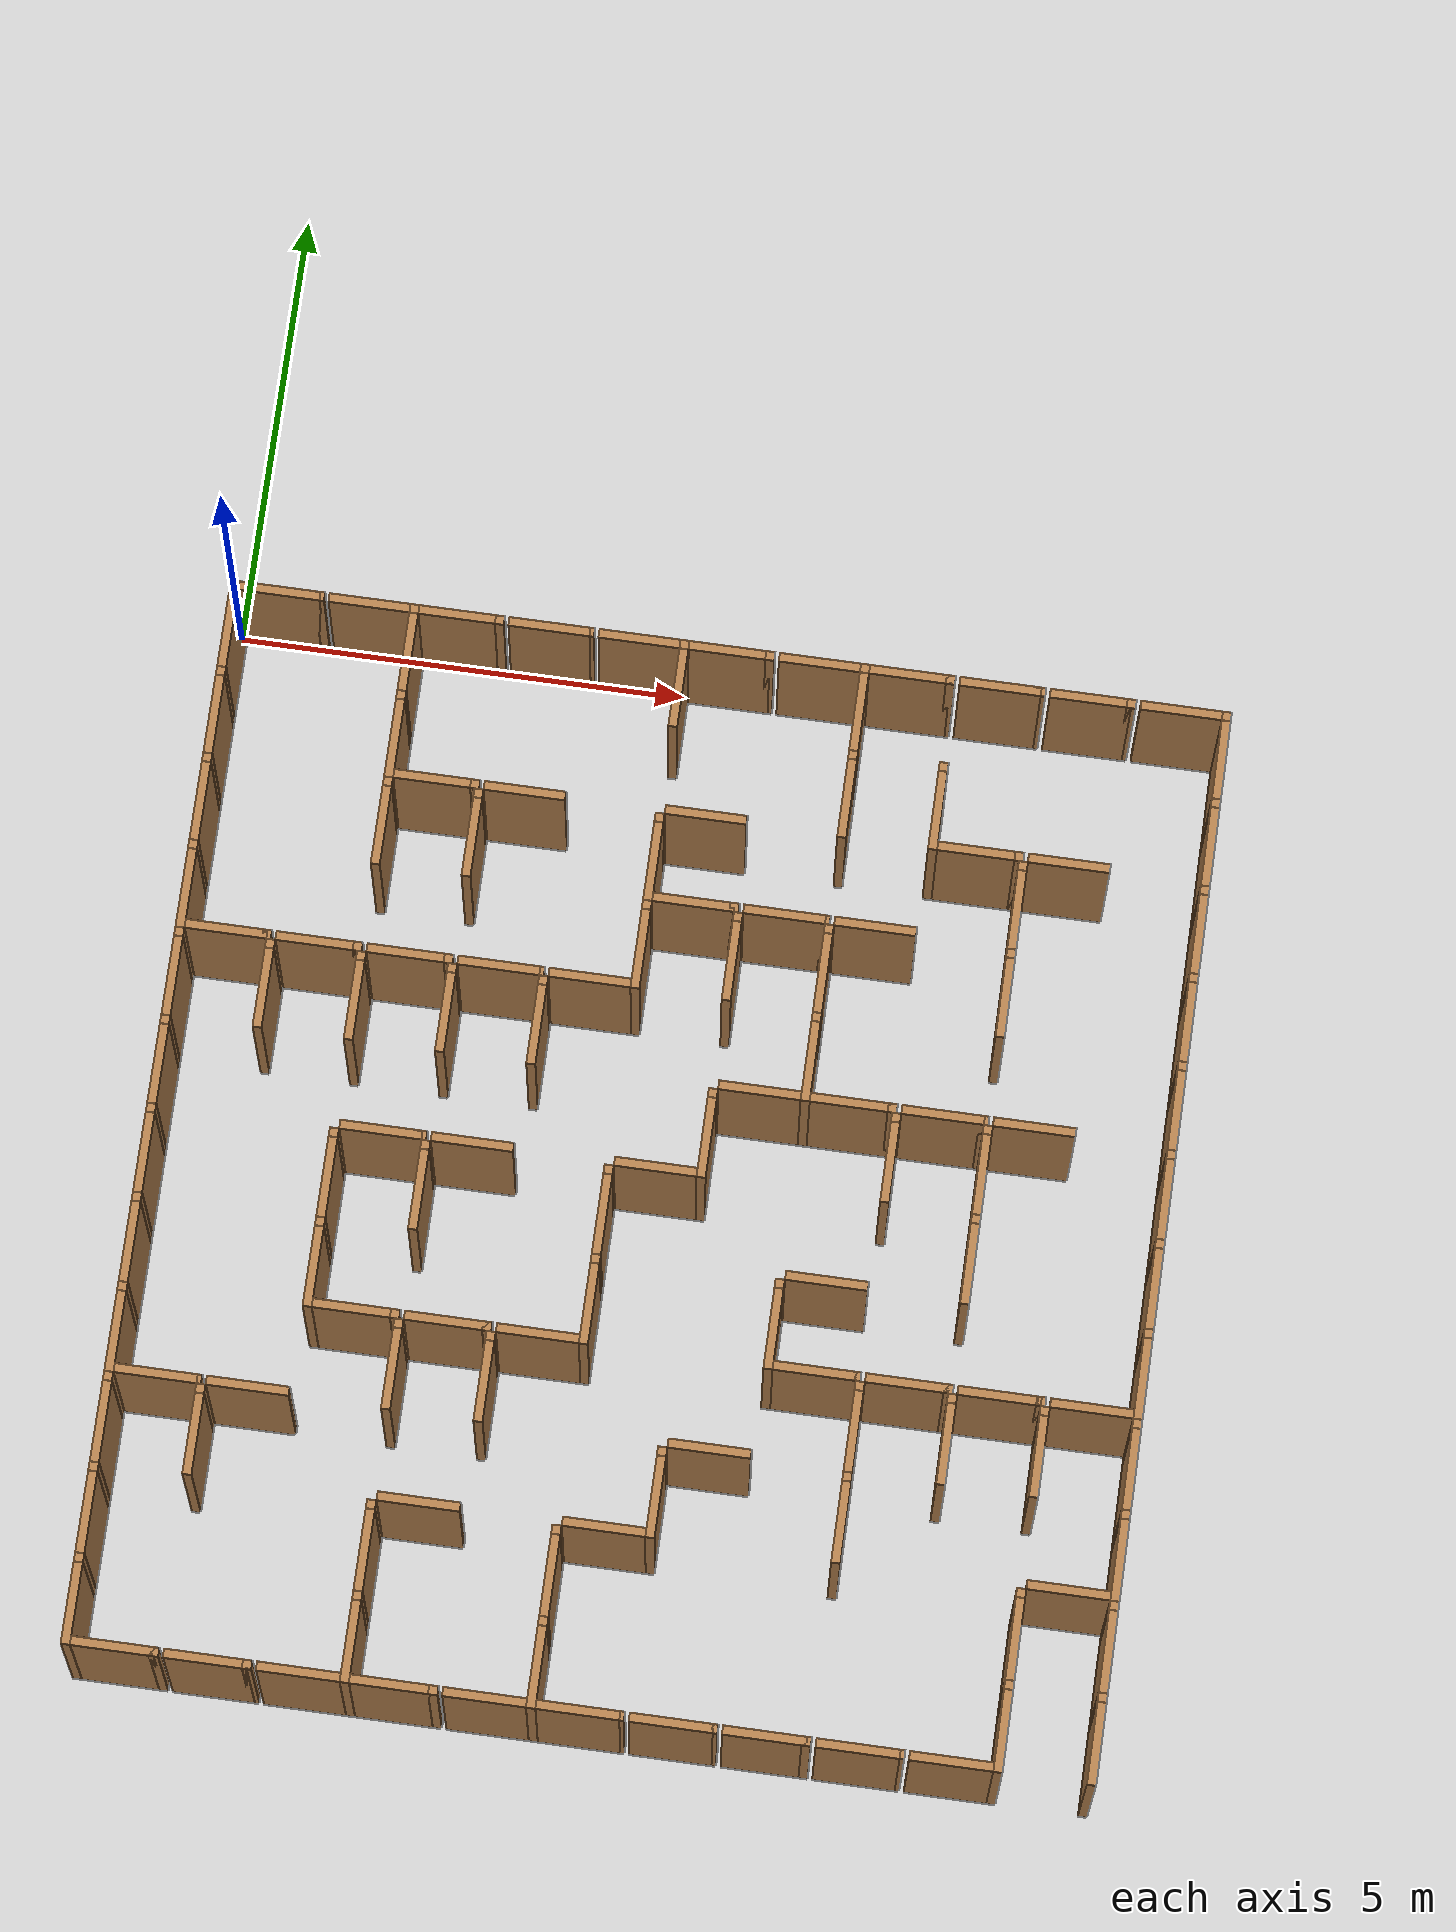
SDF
<?xml version='1.0' encoding='UTF-8'?>
<sdf version="1.6">
  <world name="default">
    <include>
      <uri>model://sun</uri>
    </include>
    <model name="ground_plane">
      <static>true</static>
      <link name="link">
        <collision name="collision">
          <geometry>
            <plane>
              <size>12.0 12.0</size>
            </plane>
          </geometry>
        </collision>
        <visual name="visual">
          <cast_shadows>false</cast_shadows>
          <geometry>
            <plane>
              <size>12.0 12.0</size>
            </plane>
          </geometry>
          <material>
            <script>
              <uri>file://media/materials/scripts/gazebo.material</uri>
              <name>Gazebo/Grey</name>
            </script>
          </material>
        </visual>
      </link>
      <pose>6.0 -6.0 0 0 0 0</pose>
    </model>
    <model name="vwall_0_0">
      <pose>0.0 -0.5 1.0 0 0 0</pose>
      <link name="link">
        <collision name="collision">
          <geometry>
            <box>
              <size>0.1 0.9 2</size>
            </box>
          </geometry>
        </collision>
        <visual name="visual">
          <geometry>
            <box>
              <size>0.1 0.9 2</size>
            </box>
          </geometry>
          <material>
            <script>
              <uri>file://media/materials/scripts/gazebo.material</uri>
              <name>Gazebo/Wood</name>
            </script>
          </material>
        </visual>
      </link>
    </model>
    <model name="joint_0.0_0.0">
      <pose>0.0 0.0 1.0 0 0 0</pose>
      <link name="link">
        <collision name="collision">
          <geometry>
            <box>
              <size>0.1 0.1 2</size>
            </box>
          </geometry>
        </collision>
        <visual name="visual">
          <geometry>
            <box>
              <size>0.1 0.1 2</size>
            </box>
          </geometry>
          <material>
            <script>
              <uri>file://media/materials/scripts/gazebo.material</uri>
              <name>Gazebo/Wood</name>
            </script>
          </material>
        </visual>
      </link>
    </model>
    <model name="vwall_0_2">
      <pose>2.0 -0.5 1.0 0 0 0</pose>
      <link name="link">
        <collision name="collision">
          <geometry>
            <box>
              <size>0.1 0.9 2</size>
            </box>
          </geometry>
        </collision>
        <visual name="visual">
          <geometry>
            <box>
              <size>0.1 0.9 2</size>
            </box>
          </geometry>
          <material>
            <script>
              <uri>file://media/materials/scripts/gazebo.material</uri>
              <name>Gazebo/Wood</name>
            </script>
          </material>
        </visual>
      </link>
    </model>
    <model name="joint_2.0_0.0">
      <pose>2.0 0.0 1.0 0 0 0</pose>
      <link name="link">
        <collision name="collision">
          <geometry>
            <box>
              <size>0.1 0.1 2</size>
            </box>
          </geometry>
        </collision>
        <visual name="visual">
          <geometry>
            <box>
              <size>0.1 0.1 2</size>
            </box>
          </geometry>
          <material>
            <script>
              <uri>file://media/materials/scripts/gazebo.material</uri>
              <name>Gazebo/Wood</name>
            </script>
          </material>
        </visual>
      </link>
    </model>
    <model name="vwall_0_5">
      <pose>5.0 -0.5 1.0 0 0 0</pose>
      <link name="link">
        <collision name="collision">
          <geometry>
            <box>
              <size>0.1 0.9 2</size>
            </box>
          </geometry>
        </collision>
        <visual name="visual">
          <geometry>
            <box>
              <size>0.1 0.9 2</size>
            </box>
          </geometry>
          <material>
            <script>
              <uri>file://media/materials/scripts/gazebo.material</uri>
              <name>Gazebo/Wood</name>
            </script>
          </material>
        </visual>
      </link>
    </model>
    <model name="joint_5.0_0.0">
      <pose>5.0 0.0 1.0 0 0 0</pose>
      <link name="link">
        <collision name="collision">
          <geometry>
            <box>
              <size>0.1 0.1 2</size>
            </box>
          </geometry>
        </collision>
        <visual name="visual">
          <geometry>
            <box>
              <size>0.1 0.1 2</size>
            </box>
          </geometry>
          <material>
            <script>
              <uri>file://media/materials/scripts/gazebo.material</uri>
              <name>Gazebo/Wood</name>
            </script>
          </material>
        </visual>
      </link>
    </model>
    <model name="vwall_0_7">
      <pose>7.0 -0.5 1.0 0 0 0</pose>
      <link name="link">
        <collision name="collision">
          <geometry>
            <box>
              <size>0.1 0.9 2</size>
            </box>
          </geometry>
        </collision>
        <visual name="visual">
          <geometry>
            <box>
              <size>0.1 0.9 2</size>
            </box>
          </geometry>
          <material>
            <script>
              <uri>file://media/materials/scripts/gazebo.material</uri>
              <name>Gazebo/Wood</name>
            </script>
          </material>
        </visual>
      </link>
    </model>
    <model name="joint_7.0_0.0">
      <pose>7.0 0.0 1.0 0 0 0</pose>
      <link name="link">
        <collision name="collision">
          <geometry>
            <box>
              <size>0.1 0.1 2</size>
            </box>
          </geometry>
        </collision>
        <visual name="visual">
          <geometry>
            <box>
              <size>0.1 0.1 2</size>
            </box>
          </geometry>
          <material>
            <script>
              <uri>file://media/materials/scripts/gazebo.material</uri>
              <name>Gazebo/Wood</name>
            </script>
          </material>
        </visual>
      </link>
    </model>
    <model name="vwall_0_11">
      <pose>11.0 -0.5 1.0 0 0 0</pose>
      <link name="link">
        <collision name="collision">
          <geometry>
            <box>
              <size>0.1 0.9 2</size>
            </box>
          </geometry>
        </collision>
        <visual name="visual">
          <geometry>
            <box>
              <size>0.1 0.9 2</size>
            </box>
          </geometry>
          <material>
            <script>
              <uri>file://media/materials/scripts/gazebo.material</uri>
              <name>Gazebo/Wood</name>
            </script>
          </material>
        </visual>
      </link>
    </model>
    <model name="joint_11.0_0.0">
      <pose>11.0 0.0 1.0 0 0 0</pose>
      <link name="link">
        <collision name="collision">
          <geometry>
            <box>
              <size>0.1 0.1 2</size>
            </box>
          </geometry>
        </collision>
        <visual name="visual">
          <geometry>
            <box>
              <size>0.1 0.1 2</size>
            </box>
          </geometry>
          <material>
            <script>
              <uri>file://media/materials/scripts/gazebo.material</uri>
              <name>Gazebo/Wood</name>
            </script>
          </material>
        </visual>
      </link>
    </model>
    <model name="vwall_1_0">
      <pose>0.0 -1.5 1.0 0 0 0</pose>
      <link name="link">
        <collision name="collision">
          <geometry>
            <box>
              <size>0.1 0.9 2</size>
            </box>
          </geometry>
        </collision>
        <visual name="visual">
          <geometry>
            <box>
              <size>0.1 0.9 2</size>
            </box>
          </geometry>
          <material>
            <script>
              <uri>file://media/materials/scripts/gazebo.material</uri>
              <name>Gazebo/Wood</name>
            </script>
          </material>
        </visual>
      </link>
    </model>
    <model name="joint_0.0_-1.0">
      <pose>0.0 -1.0 1.0 0 0 0</pose>
      <link name="link">
        <collision name="collision">
          <geometry>
            <box>
              <size>0.1 0.1 2</size>
            </box>
          </geometry>
        </collision>
        <visual name="visual">
          <geometry>
            <box>
              <size>0.1 0.1 2</size>
            </box>
          </geometry>
          <material>
            <script>
              <uri>file://media/materials/scripts/gazebo.material</uri>
              <name>Gazebo/Wood</name>
            </script>
          </material>
        </visual>
      </link>
    </model>
    <model name="vwall_1_2">
      <pose>2.0 -1.5 1.0 0 0 0</pose>
      <link name="link">
        <collision name="collision">
          <geometry>
            <box>
              <size>0.1 0.9 2</size>
            </box>
          </geometry>
        </collision>
        <visual name="visual">
          <geometry>
            <box>
              <size>0.1 0.9 2</size>
            </box>
          </geometry>
          <material>
            <script>
              <uri>file://media/materials/scripts/gazebo.material</uri>
              <name>Gazebo/Wood</name>
            </script>
          </material>
        </visual>
      </link>
    </model>
    <model name="joint_2.0_-1.0">
      <pose>2.0 -1.0 1.0 0 0 0</pose>
      <link name="link">
        <collision name="collision">
          <geometry>
            <box>
              <size>0.1 0.1 2</size>
            </box>
          </geometry>
        </collision>
        <visual name="visual">
          <geometry>
            <box>
              <size>0.1 0.1 2</size>
            </box>
          </geometry>
          <material>
            <script>
              <uri>file://media/materials/scripts/gazebo.material</uri>
              <name>Gazebo/Wood</name>
            </script>
          </material>
        </visual>
      </link>
    </model>
    <model name="vwall_1_7">
      <pose>7.0 -1.5 1.0 0 0 0</pose>
      <link name="link">
        <collision name="collision">
          <geometry>
            <box>
              <size>0.1 0.9 2</size>
            </box>
          </geometry>
        </collision>
        <visual name="visual">
          <geometry>
            <box>
              <size>0.1 0.9 2</size>
            </box>
          </geometry>
          <material>
            <script>
              <uri>file://media/materials/scripts/gazebo.material</uri>
              <name>Gazebo/Wood</name>
            </script>
          </material>
        </visual>
      </link>
    </model>
    <model name="joint_7.0_-1.0">
      <pose>7.0 -1.0 1.0 0 0 0</pose>
      <link name="link">
        <collision name="collision">
          <geometry>
            <box>
              <size>0.1 0.1 2</size>
            </box>
          </geometry>
        </collision>
        <visual name="visual">
          <geometry>
            <box>
              <size>0.1 0.1 2</size>
            </box>
          </geometry>
          <material>
            <script>
              <uri>file://media/materials/scripts/gazebo.material</uri>
              <name>Gazebo/Wood</name>
            </script>
          </material>
        </visual>
      </link>
    </model>
    <model name="vwall_1_8">
      <pose>8.0 -1.5 1.0 0 0 0</pose>
      <link name="link">
        <collision name="collision">
          <geometry>
            <box>
              <size>0.1 0.9 2</size>
            </box>
          </geometry>
        </collision>
        <visual name="visual">
          <geometry>
            <box>
              <size>0.1 0.9 2</size>
            </box>
          </geometry>
          <material>
            <script>
              <uri>file://media/materials/scripts/gazebo.material</uri>
              <name>Gazebo/Wood</name>
            </script>
          </material>
        </visual>
      </link>
    </model>
    <model name="joint_8.0_-1.0">
      <pose>8.0 -1.0 1.0 0 0 0</pose>
      <link name="link">
        <collision name="collision">
          <geometry>
            <box>
              <size>0.1 0.1 2</size>
            </box>
          </geometry>
        </collision>
        <visual name="visual">
          <geometry>
            <box>
              <size>0.1 0.1 2</size>
            </box>
          </geometry>
          <material>
            <script>
              <uri>file://media/materials/scripts/gazebo.material</uri>
              <name>Gazebo/Wood</name>
            </script>
          </material>
        </visual>
      </link>
    </model>
    <model name="vwall_1_11">
      <pose>11.0 -1.5 1.0 0 0 0</pose>
      <link name="link">
        <collision name="collision">
          <geometry>
            <box>
              <size>0.1 0.9 2</size>
            </box>
          </geometry>
        </collision>
        <visual name="visual">
          <geometry>
            <box>
              <size>0.1 0.9 2</size>
            </box>
          </geometry>
          <material>
            <script>
              <uri>file://media/materials/scripts/gazebo.material</uri>
              <name>Gazebo/Wood</name>
            </script>
          </material>
        </visual>
      </link>
    </model>
    <model name="joint_11.0_-1.0">
      <pose>11.0 -1.0 1.0 0 0 0</pose>
      <link name="link">
        <collision name="collision">
          <geometry>
            <box>
              <size>0.1 0.1 2</size>
            </box>
          </geometry>
        </collision>
        <visual name="visual">
          <geometry>
            <box>
              <size>0.1 0.1 2</size>
            </box>
          </geometry>
          <material>
            <script>
              <uri>file://media/materials/scripts/gazebo.material</uri>
              <name>Gazebo/Wood</name>
            </script>
          </material>
        </visual>
      </link>
    </model>
    <model name="vwall_2_0">
      <pose>0.0 -2.5 1.0 0 0 0</pose>
      <link name="link">
        <collision name="collision">
          <geometry>
            <box>
              <size>0.1 0.9 2</size>
            </box>
          </geometry>
        </collision>
        <visual name="visual">
          <geometry>
            <box>
              <size>0.1 0.9 2</size>
            </box>
          </geometry>
          <material>
            <script>
              <uri>file://media/materials/scripts/gazebo.material</uri>
              <name>Gazebo/Wood</name>
            </script>
          </material>
        </visual>
      </link>
    </model>
    <model name="joint_0.0_-2.0">
      <pose>0.0 -2.0 1.0 0 0 0</pose>
      <link name="link">
        <collision name="collision">
          <geometry>
            <box>
              <size>0.1 0.1 2</size>
            </box>
          </geometry>
        </collision>
        <visual name="visual">
          <geometry>
            <box>
              <size>0.1 0.1 2</size>
            </box>
          </geometry>
          <material>
            <script>
              <uri>file://media/materials/scripts/gazebo.material</uri>
              <name>Gazebo/Wood</name>
            </script>
          </material>
        </visual>
      </link>
    </model>
    <model name="vwall_2_2">
      <pose>2.0 -2.5 1.0 0 0 0</pose>
      <link name="link">
        <collision name="collision">
          <geometry>
            <box>
              <size>0.1 0.9 2</size>
            </box>
          </geometry>
        </collision>
        <visual name="visual">
          <geometry>
            <box>
              <size>0.1 0.9 2</size>
            </box>
          </geometry>
          <material>
            <script>
              <uri>file://media/materials/scripts/gazebo.material</uri>
              <name>Gazebo/Wood</name>
            </script>
          </material>
        </visual>
      </link>
    </model>
    <model name="joint_2.0_-2.0">
      <pose>2.0 -2.0 1.0 0 0 0</pose>
      <link name="link">
        <collision name="collision">
          <geometry>
            <box>
              <size>0.1 0.1 2</size>
            </box>
          </geometry>
        </collision>
        <visual name="visual">
          <geometry>
            <box>
              <size>0.1 0.1 2</size>
            </box>
          </geometry>
          <material>
            <script>
              <uri>file://media/materials/scripts/gazebo.material</uri>
              <name>Gazebo/Wood</name>
            </script>
          </material>
        </visual>
      </link>
    </model>
    <model name="vwall_2_3">
      <pose>3.0 -2.5 1.0 0 0 0</pose>
      <link name="link">
        <collision name="collision">
          <geometry>
            <box>
              <size>0.1 0.9 2</size>
            </box>
          </geometry>
        </collision>
        <visual name="visual">
          <geometry>
            <box>
              <size>0.1 0.9 2</size>
            </box>
          </geometry>
          <material>
            <script>
              <uri>file://media/materials/scripts/gazebo.material</uri>
              <name>Gazebo/Wood</name>
            </script>
          </material>
        </visual>
      </link>
    </model>
    <model name="joint_3.0_-2.0">
      <pose>3.0 -2.0 1.0 0 0 0</pose>
      <link name="link">
        <collision name="collision">
          <geometry>
            <box>
              <size>0.1 0.1 2</size>
            </box>
          </geometry>
        </collision>
        <visual name="visual">
          <geometry>
            <box>
              <size>0.1 0.1 2</size>
            </box>
          </geometry>
          <material>
            <script>
              <uri>file://media/materials/scripts/gazebo.material</uri>
              <name>Gazebo/Wood</name>
            </script>
          </material>
        </visual>
      </link>
    </model>
    <model name="vwall_2_5">
      <pose>5.0 -2.5 1.0 0 0 0</pose>
      <link name="link">
        <collision name="collision">
          <geometry>
            <box>
              <size>0.1 0.9 2</size>
            </box>
          </geometry>
        </collision>
        <visual name="visual">
          <geometry>
            <box>
              <size>0.1 0.9 2</size>
            </box>
          </geometry>
          <material>
            <script>
              <uri>file://media/materials/scripts/gazebo.material</uri>
              <name>Gazebo/Wood</name>
            </script>
          </material>
        </visual>
      </link>
    </model>
    <model name="joint_5.0_-2.0">
      <pose>5.0 -2.0 1.0 0 0 0</pose>
      <link name="link">
        <collision name="collision">
          <geometry>
            <box>
              <size>0.1 0.1 2</size>
            </box>
          </geometry>
        </collision>
        <visual name="visual">
          <geometry>
            <box>
              <size>0.1 0.1 2</size>
            </box>
          </geometry>
          <material>
            <script>
              <uri>file://media/materials/scripts/gazebo.material</uri>
              <name>Gazebo/Wood</name>
            </script>
          </material>
        </visual>
      </link>
    </model>
    <model name="vwall_2_9">
      <pose>9.0 -2.5 1.0 0 0 0</pose>
      <link name="link">
        <collision name="collision">
          <geometry>
            <box>
              <size>0.1 0.9 2</size>
            </box>
          </geometry>
        </collision>
        <visual name="visual">
          <geometry>
            <box>
              <size>0.1 0.9 2</size>
            </box>
          </geometry>
          <material>
            <script>
              <uri>file://media/materials/scripts/gazebo.material</uri>
              <name>Gazebo/Wood</name>
            </script>
          </material>
        </visual>
      </link>
    </model>
    <model name="joint_9.0_-2.0">
      <pose>9.0 -2.0 1.0 0 0 0</pose>
      <link name="link">
        <collision name="collision">
          <geometry>
            <box>
              <size>0.1 0.1 2</size>
            </box>
          </geometry>
        </collision>
        <visual name="visual">
          <geometry>
            <box>
              <size>0.1 0.1 2</size>
            </box>
          </geometry>
          <material>
            <script>
              <uri>file://media/materials/scripts/gazebo.material</uri>
              <name>Gazebo/Wood</name>
            </script>
          </material>
        </visual>
      </link>
    </model>
    <model name="vwall_2_11">
      <pose>11.0 -2.5 1.0 0 0 0</pose>
      <link name="link">
        <collision name="collision">
          <geometry>
            <box>
              <size>0.1 0.9 2</size>
            </box>
          </geometry>
        </collision>
        <visual name="visual">
          <geometry>
            <box>
              <size>0.1 0.9 2</size>
            </box>
          </geometry>
          <material>
            <script>
              <uri>file://media/materials/scripts/gazebo.material</uri>
              <name>Gazebo/Wood</name>
            </script>
          </material>
        </visual>
      </link>
    </model>
    <model name="joint_11.0_-2.0">
      <pose>11.0 -2.0 1.0 0 0 0</pose>
      <link name="link">
        <collision name="collision">
          <geometry>
            <box>
              <size>0.1 0.1 2</size>
            </box>
          </geometry>
        </collision>
        <visual name="visual">
          <geometry>
            <box>
              <size>0.1 0.1 2</size>
            </box>
          </geometry>
          <material>
            <script>
              <uri>file://media/materials/scripts/gazebo.material</uri>
              <name>Gazebo/Wood</name>
            </script>
          </material>
        </visual>
      </link>
    </model>
    <model name="vwall_3_0">
      <pose>0.0 -3.5 1.0 0 0 0</pose>
      <link name="link">
        <collision name="collision">
          <geometry>
            <box>
              <size>0.1 0.9 2</size>
            </box>
          </geometry>
        </collision>
        <visual name="visual">
          <geometry>
            <box>
              <size>0.1 0.9 2</size>
            </box>
          </geometry>
          <material>
            <script>
              <uri>file://media/materials/scripts/gazebo.material</uri>
              <name>Gazebo/Wood</name>
            </script>
          </material>
        </visual>
      </link>
    </model>
    <model name="joint_0.0_-3.0">
      <pose>0.0 -3.0 1.0 0 0 0</pose>
      <link name="link">
        <collision name="collision">
          <geometry>
            <box>
              <size>0.1 0.1 2</size>
            </box>
          </geometry>
        </collision>
        <visual name="visual">
          <geometry>
            <box>
              <size>0.1 0.1 2</size>
            </box>
          </geometry>
          <material>
            <script>
              <uri>file://media/materials/scripts/gazebo.material</uri>
              <name>Gazebo/Wood</name>
            </script>
          </material>
        </visual>
      </link>
    </model>
    <model name="vwall_3_5">
      <pose>5.0 -3.5 1.0 0 0 0</pose>
      <link name="link">
        <collision name="collision">
          <geometry>
            <box>
              <size>0.1 0.9 2</size>
            </box>
          </geometry>
        </collision>
        <visual name="visual">
          <geometry>
            <box>
              <size>0.1 0.9 2</size>
            </box>
          </geometry>
          <material>
            <script>
              <uri>file://media/materials/scripts/gazebo.material</uri>
              <name>Gazebo/Wood</name>
            </script>
          </material>
        </visual>
      </link>
    </model>
    <model name="joint_5.0_-3.0">
      <pose>5.0 -3.0 1.0 0 0 0</pose>
      <link name="link">
        <collision name="collision">
          <geometry>
            <box>
              <size>0.1 0.1 2</size>
            </box>
          </geometry>
        </collision>
        <visual name="visual">
          <geometry>
            <box>
              <size>0.1 0.1 2</size>
            </box>
          </geometry>
          <material>
            <script>
              <uri>file://media/materials/scripts/gazebo.material</uri>
              <name>Gazebo/Wood</name>
            </script>
          </material>
        </visual>
      </link>
    </model>
    <model name="vwall_3_6">
      <pose>6.0 -3.5 1.0 0 0 0</pose>
      <link name="link">
        <collision name="collision">
          <geometry>
            <box>
              <size>0.1 0.9 2</size>
            </box>
          </geometry>
        </collision>
        <visual name="visual">
          <geometry>
            <box>
              <size>0.1 0.9 2</size>
            </box>
          </geometry>
          <material>
            <script>
              <uri>file://media/materials/scripts/gazebo.material</uri>
              <name>Gazebo/Wood</name>
            </script>
          </material>
        </visual>
      </link>
    </model>
    <model name="joint_6.0_-3.0">
      <pose>6.0 -3.0 1.0 0 0 0</pose>
      <link name="link">
        <collision name="collision">
          <geometry>
            <box>
              <size>0.1 0.1 2</size>
            </box>
          </geometry>
        </collision>
        <visual name="visual">
          <geometry>
            <box>
              <size>0.1 0.1 2</size>
            </box>
          </geometry>
          <material>
            <script>
              <uri>file://media/materials/scripts/gazebo.material</uri>
              <name>Gazebo/Wood</name>
            </script>
          </material>
        </visual>
      </link>
    </model>
    <model name="vwall_3_7">
      <pose>7.0 -3.5 1.0 0 0 0</pose>
      <link name="link">
        <collision name="collision">
          <geometry>
            <box>
              <size>0.1 0.9 2</size>
            </box>
          </geometry>
        </collision>
        <visual name="visual">
          <geometry>
            <box>
              <size>0.1 0.9 2</size>
            </box>
          </geometry>
          <material>
            <script>
              <uri>file://media/materials/scripts/gazebo.material</uri>
              <name>Gazebo/Wood</name>
            </script>
          </material>
        </visual>
      </link>
    </model>
    <model name="joint_7.0_-3.0">
      <pose>7.0 -3.0 1.0 0 0 0</pose>
      <link name="link">
        <collision name="collision">
          <geometry>
            <box>
              <size>0.1 0.1 2</size>
            </box>
          </geometry>
        </collision>
        <visual name="visual">
          <geometry>
            <box>
              <size>0.1 0.1 2</size>
            </box>
          </geometry>
          <material>
            <script>
              <uri>file://media/materials/scripts/gazebo.material</uri>
              <name>Gazebo/Wood</name>
            </script>
          </material>
        </visual>
      </link>
    </model>
    <model name="vwall_3_9">
      <pose>9.0 -3.5 1.0 0 0 0</pose>
      <link name="link">
        <collision name="collision">
          <geometry>
            <box>
              <size>0.1 0.9 2</size>
            </box>
          </geometry>
        </collision>
        <visual name="visual">
          <geometry>
            <box>
              <size>0.1 0.9 2</size>
            </box>
          </geometry>
          <material>
            <script>
              <uri>file://media/materials/scripts/gazebo.material</uri>
              <name>Gazebo/Wood</name>
            </script>
          </material>
        </visual>
      </link>
    </model>
    <model name="joint_9.0_-3.0">
      <pose>9.0 -3.0 1.0 0 0 0</pose>
      <link name="link">
        <collision name="collision">
          <geometry>
            <box>
              <size>0.1 0.1 2</size>
            </box>
          </geometry>
        </collision>
        <visual name="visual">
          <geometry>
            <box>
              <size>0.1 0.1 2</size>
            </box>
          </geometry>
          <material>
            <script>
              <uri>file://media/materials/scripts/gazebo.material</uri>
              <name>Gazebo/Wood</name>
            </script>
          </material>
        </visual>
      </link>
    </model>
    <model name="vwall_3_11">
      <pose>11.0 -3.5 1.0 0 0 0</pose>
      <link name="link">
        <collision name="collision">
          <geometry>
            <box>
              <size>0.1 0.9 2</size>
            </box>
          </geometry>
        </collision>
        <visual name="visual">
          <geometry>
            <box>
              <size>0.1 0.9 2</size>
            </box>
          </geometry>
          <material>
            <script>
              <uri>file://media/materials/scripts/gazebo.material</uri>
              <name>Gazebo/Wood</name>
            </script>
          </material>
        </visual>
      </link>
    </model>
    <model name="joint_11.0_-3.0">
      <pose>11.0 -3.0 1.0 0 0 0</pose>
      <link name="link">
        <collision name="collision">
          <geometry>
            <box>
              <size>0.1 0.1 2</size>
            </box>
          </geometry>
        </collision>
        <visual name="visual">
          <geometry>
            <box>
              <size>0.1 0.1 2</size>
            </box>
          </geometry>
          <material>
            <script>
              <uri>file://media/materials/scripts/gazebo.material</uri>
              <name>Gazebo/Wood</name>
            </script>
          </material>
        </visual>
      </link>
    </model>
    <model name="vwall_4_0">
      <pose>0.0 -4.5 1.0 0 0 0</pose>
      <link name="link">
        <collision name="collision">
          <geometry>
            <box>
              <size>0.1 0.9 2</size>
            </box>
          </geometry>
        </collision>
        <visual name="visual">
          <geometry>
            <box>
              <size>0.1 0.9 2</size>
            </box>
          </geometry>
          <material>
            <script>
              <uri>file://media/materials/scripts/gazebo.material</uri>
              <name>Gazebo/Wood</name>
            </script>
          </material>
        </visual>
      </link>
    </model>
    <model name="joint_0.0_-4.0">
      <pose>0.0 -4.0 1.0 0 0 0</pose>
      <link name="link">
        <collision name="collision">
          <geometry>
            <box>
              <size>0.1 0.1 2</size>
            </box>
          </geometry>
        </collision>
        <visual name="visual">
          <geometry>
            <box>
              <size>0.1 0.1 2</size>
            </box>
          </geometry>
          <material>
            <script>
              <uri>file://media/materials/scripts/gazebo.material</uri>
              <name>Gazebo/Wood</name>
            </script>
          </material>
        </visual>
      </link>
    </model>
    <model name="vwall_4_1">
      <pose>1.0 -4.5 1.0 0 0 0</pose>
      <link name="link">
        <collision name="collision">
          <geometry>
            <box>
              <size>0.1 0.9 2</size>
            </box>
          </geometry>
        </collision>
        <visual name="visual">
          <geometry>
            <box>
              <size>0.1 0.9 2</size>
            </box>
          </geometry>
          <material>
            <script>
              <uri>file://media/materials/scripts/gazebo.material</uri>
              <name>Gazebo/Wood</name>
            </script>
          </material>
        </visual>
      </link>
    </model>
    <model name="joint_1.0_-4.0">
      <pose>1.0 -4.0 1.0 0 0 0</pose>
      <link name="link">
        <collision name="collision">
          <geometry>
            <box>
              <size>0.1 0.1 2</size>
            </box>
          </geometry>
        </collision>
        <visual name="visual">
          <geometry>
            <box>
              <size>0.1 0.1 2</size>
            </box>
          </geometry>
          <material>
            <script>
              <uri>file://media/materials/scripts/gazebo.material</uri>
              <name>Gazebo/Wood</name>
            </script>
          </material>
        </visual>
      </link>
    </model>
    <model name="vwall_4_2">
      <pose>2.0 -4.5 1.0 0 0 0</pose>
      <link name="link">
        <collision name="collision">
          <geometry>
            <box>
              <size>0.1 0.9 2</size>
            </box>
          </geometry>
        </collision>
        <visual name="visual">
          <geometry>
            <box>
              <size>0.1 0.9 2</size>
            </box>
          </geometry>
          <material>
            <script>
              <uri>file://media/materials/scripts/gazebo.material</uri>
              <name>Gazebo/Wood</name>
            </script>
          </material>
        </visual>
      </link>
    </model>
    <model name="joint_2.0_-4.0">
      <pose>2.0 -4.0 1.0 0 0 0</pose>
      <link name="link">
        <collision name="collision">
          <geometry>
            <box>
              <size>0.1 0.1 2</size>
            </box>
          </geometry>
        </collision>
        <visual name="visual">
          <geometry>
            <box>
              <size>0.1 0.1 2</size>
            </box>
          </geometry>
          <material>
            <script>
              <uri>file://media/materials/scripts/gazebo.material</uri>
              <name>Gazebo/Wood</name>
            </script>
          </material>
        </visual>
      </link>
    </model>
    <model name="vwall_4_3">
      <pose>3.0 -4.5 1.0 0 0 0</pose>
      <link name="link">
        <collision name="collision">
          <geometry>
            <box>
              <size>0.1 0.9 2</size>
            </box>
          </geometry>
        </collision>
        <visual name="visual">
          <geometry>
            <box>
              <size>0.1 0.9 2</size>
            </box>
          </geometry>
          <material>
            <script>
              <uri>file://media/materials/scripts/gazebo.material</uri>
              <name>Gazebo/Wood</name>
            </script>
          </material>
        </visual>
      </link>
    </model>
    <model name="joint_3.0_-4.0">
      <pose>3.0 -4.0 1.0 0 0 0</pose>
      <link name="link">
        <collision name="collision">
          <geometry>
            <box>
              <size>0.1 0.1 2</size>
            </box>
          </geometry>
        </collision>
        <visual name="visual">
          <geometry>
            <box>
              <size>0.1 0.1 2</size>
            </box>
          </geometry>
          <material>
            <script>
              <uri>file://media/materials/scripts/gazebo.material</uri>
              <name>Gazebo/Wood</name>
            </script>
          </material>
        </visual>
      </link>
    </model>
    <model name="vwall_4_4">
      <pose>4.0 -4.5 1.0 0 0 0</pose>
      <link name="link">
        <collision name="collision">
          <geometry>
            <box>
              <size>0.1 0.9 2</size>
            </box>
          </geometry>
        </collision>
        <visual name="visual">
          <geometry>
            <box>
              <size>0.1 0.9 2</size>
            </box>
          </geometry>
          <material>
            <script>
              <uri>file://media/materials/scripts/gazebo.material</uri>
              <name>Gazebo/Wood</name>
            </script>
          </material>
        </visual>
      </link>
    </model>
    <model name="joint_4.0_-4.0">
      <pose>4.0 -4.0 1.0 0 0 0</pose>
      <link name="link">
        <collision name="collision">
          <geometry>
            <box>
              <size>0.1 0.1 2</size>
            </box>
          </geometry>
        </collision>
        <visual name="visual">
          <geometry>
            <box>
              <size>0.1 0.1 2</size>
            </box>
          </geometry>
          <material>
            <script>
              <uri>file://media/materials/scripts/gazebo.material</uri>
              <name>Gazebo/Wood</name>
            </script>
          </material>
        </visual>
      </link>
    </model>
    <model name="vwall_4_7">
      <pose>7.0 -4.5 1.0 0 0 0</pose>
      <link name="link">
        <collision name="collision">
          <geometry>
            <box>
              <size>0.1 0.9 2</size>
            </box>
          </geometry>
        </collision>
        <visual name="visual">
          <geometry>
            <box>
              <size>0.1 0.9 2</size>
            </box>
          </geometry>
          <material>
            <script>
              <uri>file://media/materials/scripts/gazebo.material</uri>
              <name>Gazebo/Wood</name>
            </script>
          </material>
        </visual>
      </link>
    </model>
    <model name="joint_7.0_-4.0">
      <pose>7.0 -4.0 1.0 0 0 0</pose>
      <link name="link">
        <collision name="collision">
          <geometry>
            <box>
              <size>0.1 0.1 2</size>
            </box>
          </geometry>
        </collision>
        <visual name="visual">
          <geometry>
            <box>
              <size>0.1 0.1 2</size>
            </box>
          </geometry>
          <material>
            <script>
              <uri>file://media/materials/scripts/gazebo.material</uri>
              <name>Gazebo/Wood</name>
            </script>
          </material>
        </visual>
      </link>
    </model>
    <model name="vwall_4_11">
      <pose>11.0 -4.5 1.0 0 0 0</pose>
      <link name="link">
        <collision name="collision">
          <geometry>
            <box>
              <size>0.1 0.9 2</size>
            </box>
          </geometry>
        </collision>
        <visual name="visual">
          <geometry>
            <box>
              <size>0.1 0.9 2</size>
            </box>
          </geometry>
          <material>
            <script>
              <uri>file://media/materials/scripts/gazebo.material</uri>
              <name>Gazebo/Wood</name>
            </script>
          </material>
        </visual>
      </link>
    </model>
    <model name="joint_11.0_-4.0">
      <pose>11.0 -4.0 1.0 0 0 0</pose>
      <link name="link">
        <collision name="collision">
          <geometry>
            <box>
              <size>0.1 0.1 2</size>
            </box>
          </geometry>
        </collision>
        <visual name="visual">
          <geometry>
            <box>
              <size>0.1 0.1 2</size>
            </box>
          </geometry>
          <material>
            <script>
              <uri>file://media/materials/scripts/gazebo.material</uri>
              <name>Gazebo/Wood</name>
            </script>
          </material>
        </visual>
      </link>
    </model>
    <model name="vwall_5_0">
      <pose>0.0 -5.5 1.0 0 0 0</pose>
      <link name="link">
        <collision name="collision">
          <geometry>
            <box>
              <size>0.1 0.9 2</size>
            </box>
          </geometry>
        </collision>
        <visual name="visual">
          <geometry>
            <box>
              <size>0.1 0.9 2</size>
            </box>
          </geometry>
          <material>
            <script>
              <uri>file://media/materials/scripts/gazebo.material</uri>
              <name>Gazebo/Wood</name>
            </script>
          </material>
        </visual>
      </link>
    </model>
    <model name="joint_0.0_-5.0">
      <pose>0.0 -5.0 1.0 0 0 0</pose>
      <link name="link">
        <collision name="collision">
          <geometry>
            <box>
              <size>0.1 0.1 2</size>
            </box>
          </geometry>
        </collision>
        <visual name="visual">
          <geometry>
            <box>
              <size>0.1 0.1 2</size>
            </box>
          </geometry>
          <material>
            <script>
              <uri>file://media/materials/scripts/gazebo.material</uri>
              <name>Gazebo/Wood</name>
            </script>
          </material>
        </visual>
      </link>
    </model>
    <model name="vwall_5_6">
      <pose>6.0 -5.5 1.0 0 0 0</pose>
      <link name="link">
        <collision name="collision">
          <geometry>
            <box>
              <size>0.1 0.9 2</size>
            </box>
          </geometry>
        </collision>
        <visual name="visual">
          <geometry>
            <box>
              <size>0.1 0.9 2</size>
            </box>
          </geometry>
          <material>
            <script>
              <uri>file://media/materials/scripts/gazebo.material</uri>
              <name>Gazebo/Wood</name>
            </script>
          </material>
        </visual>
      </link>
    </model>
    <model name="joint_6.0_-5.0">
      <pose>6.0 -5.0 1.0 0 0 0</pose>
      <link name="link">
        <collision name="collision">
          <geometry>
            <box>
              <size>0.1 0.1 2</size>
            </box>
          </geometry>
        </collision>
        <visual name="visual">
          <geometry>
            <box>
              <size>0.1 0.1 2</size>
            </box>
          </geometry>
          <material>
            <script>
              <uri>file://media/materials/scripts/gazebo.material</uri>
              <name>Gazebo/Wood</name>
            </script>
          </material>
        </visual>
      </link>
    </model>
    <model name="vwall_5_8">
      <pose>8.0 -5.5 1.0 0 0 0</pose>
      <link name="link">
        <collision name="collision">
          <geometry>
            <box>
              <size>0.1 0.9 2</size>
            </box>
          </geometry>
        </collision>
        <visual name="visual">
          <geometry>
            <box>
              <size>0.1 0.9 2</size>
            </box>
          </geometry>
          <material>
            <script>
              <uri>file://media/materials/scripts/gazebo.material</uri>
              <name>Gazebo/Wood</name>
            </script>
          </material>
        </visual>
      </link>
    </model>
    <model name="joint_8.0_-5.0">
      <pose>8.0 -5.0 1.0 0 0 0</pose>
      <link name="link">
        <collision name="collision">
          <geometry>
            <box>
              <size>0.1 0.1 2</size>
            </box>
          </geometry>
        </collision>
        <visual name="visual">
          <geometry>
            <box>
              <size>0.1 0.1 2</size>
            </box>
          </geometry>
          <material>
            <script>
              <uri>file://media/materials/scripts/gazebo.material</uri>
              <name>Gazebo/Wood</name>
            </script>
          </material>
        </visual>
      </link>
    </model>
    <model name="vwall_5_9">
      <pose>9.0 -5.5 1.0 0 0 0</pose>
      <link name="link">
        <collision name="collision">
          <geometry>
            <box>
              <size>0.1 0.9 2</size>
            </box>
          </geometry>
        </collision>
        <visual name="visual">
          <geometry>
            <box>
              <size>0.1 0.9 2</size>
            </box>
          </geometry>
          <material>
            <script>
              <uri>file://media/materials/scripts/gazebo.material</uri>
              <name>Gazebo/Wood</name>
            </script>
          </material>
        </visual>
      </link>
    </model>
    <model name="joint_9.0_-5.0">
      <pose>9.0 -5.0 1.0 0 0 0</pose>
      <link name="link">
        <collision name="collision">
          <geometry>
            <box>
              <size>0.1 0.1 2</size>
            </box>
          </geometry>
        </collision>
        <visual name="visual">
          <geometry>
            <box>
              <size>0.1 0.1 2</size>
            </box>
          </geometry>
          <material>
            <script>
              <uri>file://media/materials/scripts/gazebo.material</uri>
              <name>Gazebo/Wood</name>
            </script>
          </material>
        </visual>
      </link>
    </model>
    <model name="vwall_5_11">
      <pose>11.0 -5.5 1.0 0 0 0</pose>
      <link name="link">
        <collision name="collision">
          <geometry>
            <box>
              <size>0.1 0.9 2</size>
            </box>
          </geometry>
        </collision>
        <visual name="visual">
          <geometry>
            <box>
              <size>0.1 0.9 2</size>
            </box>
          </geometry>
          <material>
            <script>
              <uri>file://media/materials/scripts/gazebo.material</uri>
              <name>Gazebo/Wood</name>
            </script>
          </material>
        </visual>
      </link>
    </model>
    <model name="joint_11.0_-5.0">
      <pose>11.0 -5.0 1.0 0 0 0</pose>
      <link name="link">
        <collision name="collision">
          <geometry>
            <box>
              <size>0.1 0.1 2</size>
            </box>
          </geometry>
        </collision>
        <visual name="visual">
          <geometry>
            <box>
              <size>0.1 0.1 2</size>
            </box>
          </geometry>
          <material>
            <script>
              <uri>file://media/materials/scripts/gazebo.material</uri>
              <name>Gazebo/Wood</name>
            </script>
          </material>
        </visual>
      </link>
    </model>
    <model name="vwall_6_0">
      <pose>0.0 -6.5 1.0 0 0 0</pose>
      <link name="link">
        <collision name="collision">
          <geometry>
            <box>
              <size>0.1 0.9 2</size>
            </box>
          </geometry>
        </collision>
        <visual name="visual">
          <geometry>
            <box>
              <size>0.1 0.9 2</size>
            </box>
          </geometry>
          <material>
            <script>
              <uri>file://media/materials/scripts/gazebo.material</uri>
              <name>Gazebo/Wood</name>
            </script>
          </material>
        </visual>
      </link>
    </model>
    <model name="joint_0.0_-6.0">
      <pose>0.0 -6.0 1.0 0 0 0</pose>
      <link name="link">
        <collision name="collision">
          <geometry>
            <box>
              <size>0.1 0.1 2</size>
            </box>
          </geometry>
        </collision>
        <visual name="visual">
          <geometry>
            <box>
              <size>0.1 0.1 2</size>
            </box>
          </geometry>
          <material>
            <script>
              <uri>file://media/materials/scripts/gazebo.material</uri>
              <name>Gazebo/Wood</name>
            </script>
          </material>
        </visual>
      </link>
    </model>
    <model name="vwall_6_2">
      <pose>2.0 -6.5 1.0 0 0 0</pose>
      <link name="link">
        <collision name="collision">
          <geometry>
            <box>
              <size>0.1 0.9 2</size>
            </box>
          </geometry>
        </collision>
        <visual name="visual">
          <geometry>
            <box>
              <size>0.1 0.9 2</size>
            </box>
          </geometry>
          <material>
            <script>
              <uri>file://media/materials/scripts/gazebo.material</uri>
              <name>Gazebo/Wood</name>
            </script>
          </material>
        </visual>
      </link>
    </model>
    <model name="joint_2.0_-6.0">
      <pose>2.0 -6.0 1.0 0 0 0</pose>
      <link name="link">
        <collision name="collision">
          <geometry>
            <box>
              <size>0.1 0.1 2</size>
            </box>
          </geometry>
        </collision>
        <visual name="visual">
          <geometry>
            <box>
              <size>0.1 0.1 2</size>
            </box>
          </geometry>
          <material>
            <script>
              <uri>file://media/materials/scripts/gazebo.material</uri>
              <name>Gazebo/Wood</name>
            </script>
          </material>
        </visual>
      </link>
    </model>
    <model name="vwall_6_3">
      <pose>3.0 -6.5 1.0 0 0 0</pose>
      <link name="link">
        <collision name="collision">
          <geometry>
            <box>
              <size>0.1 0.9 2</size>
            </box>
          </geometry>
        </collision>
        <visual name="visual">
          <geometry>
            <box>
              <size>0.1 0.9 2</size>
            </box>
          </geometry>
          <material>
            <script>
              <uri>file://media/materials/scripts/gazebo.material</uri>
              <name>Gazebo/Wood</name>
            </script>
          </material>
        </visual>
      </link>
    </model>
    <model name="joint_3.0_-6.0">
      <pose>3.0 -6.0 1.0 0 0 0</pose>
      <link name="link">
        <collision name="collision">
          <geometry>
            <box>
              <size>0.1 0.1 2</size>
            </box>
          </geometry>
        </collision>
        <visual name="visual">
          <geometry>
            <box>
              <size>0.1 0.1 2</size>
            </box>
          </geometry>
          <material>
            <script>
              <uri>file://media/materials/scripts/gazebo.material</uri>
              <name>Gazebo/Wood</name>
            </script>
          </material>
        </visual>
      </link>
    </model>
    <model name="vwall_6_5">
      <pose>5.0 -6.5 1.0 0 0 0</pose>
      <link name="link">
        <collision name="collision">
          <geometry>
            <box>
              <size>0.1 0.9 2</size>
            </box>
          </geometry>
        </collision>
        <visual name="visual">
          <geometry>
            <box>
              <size>0.1 0.9 2</size>
            </box>
          </geometry>
          <material>
            <script>
              <uri>file://media/materials/scripts/gazebo.material</uri>
              <name>Gazebo/Wood</name>
            </script>
          </material>
        </visual>
      </link>
    </model>
    <model name="joint_5.0_-6.0">
      <pose>5.0 -6.0 1.0 0 0 0</pose>
      <link name="link">
        <collision name="collision">
          <geometry>
            <box>
              <size>0.1 0.1 2</size>
            </box>
          </geometry>
        </collision>
        <visual name="visual">
          <geometry>
            <box>
              <size>0.1 0.1 2</size>
            </box>
          </geometry>
          <material>
            <script>
              <uri>file://media/materials/scripts/gazebo.material</uri>
              <name>Gazebo/Wood</name>
            </script>
          </material>
        </visual>
      </link>
    </model>
    <model name="vwall_6_9">
      <pose>9.0 -6.5 1.0 0 0 0</pose>
      <link name="link">
        <collision name="collision">
          <geometry>
            <box>
              <size>0.1 0.9 2</size>
            </box>
          </geometry>
        </collision>
        <visual name="visual">
          <geometry>
            <box>
              <size>0.1 0.9 2</size>
            </box>
          </geometry>
          <material>
            <script>
              <uri>file://media/materials/scripts/gazebo.material</uri>
              <name>Gazebo/Wood</name>
            </script>
          </material>
        </visual>
      </link>
    </model>
    <model name="joint_9.0_-6.0">
      <pose>9.0 -6.0 1.0 0 0 0</pose>
      <link name="link">
        <collision name="collision">
          <geometry>
            <box>
              <size>0.1 0.1 2</size>
            </box>
          </geometry>
        </collision>
        <visual name="visual">
          <geometry>
            <box>
              <size>0.1 0.1 2</size>
            </box>
          </geometry>
          <material>
            <script>
              <uri>file://media/materials/scripts/gazebo.material</uri>
              <name>Gazebo/Wood</name>
            </script>
          </material>
        </visual>
      </link>
    </model>
    <model name="vwall_6_11">
      <pose>11.0 -6.5 1.0 0 0 0</pose>
      <link name="link">
        <collision name="collision">
          <geometry>
            <box>
              <size>0.1 0.9 2</size>
            </box>
          </geometry>
        </collision>
        <visual name="visual">
          <geometry>
            <box>
              <size>0.1 0.9 2</size>
            </box>
          </geometry>
          <material>
            <script>
              <uri>file://media/materials/scripts/gazebo.material</uri>
              <name>Gazebo/Wood</name>
            </script>
          </material>
        </visual>
      </link>
    </model>
    <model name="joint_11.0_-6.0">
      <pose>11.0 -6.0 1.0 0 0 0</pose>
      <link name="link">
        <collision name="collision">
          <geometry>
            <box>
              <size>0.1 0.1 2</size>
            </box>
          </geometry>
        </collision>
        <visual name="visual">
          <geometry>
            <box>
              <size>0.1 0.1 2</size>
            </box>
          </geometry>
          <material>
            <script>
              <uri>file://media/materials/scripts/gazebo.material</uri>
              <name>Gazebo/Wood</name>
            </script>
          </material>
        </visual>
      </link>
    </model>
    <model name="vwall_7_0">
      <pose>0.0 -7.5 1.0 0 0 0</pose>
      <link name="link">
        <collision name="collision">
          <geometry>
            <box>
              <size>0.1 0.9 2</size>
            </box>
          </geometry>
        </collision>
        <visual name="visual">
          <geometry>
            <box>
              <size>0.1 0.9 2</size>
            </box>
          </geometry>
          <material>
            <script>
              <uri>file://media/materials/scripts/gazebo.material</uri>
              <name>Gazebo/Wood</name>
            </script>
          </material>
        </visual>
      </link>
    </model>
    <model name="joint_0.0_-7.0">
      <pose>0.0 -7.0 1.0 0 0 0</pose>
      <link name="link">
        <collision name="collision">
          <geometry>
            <box>
              <size>0.1 0.1 2</size>
            </box>
          </geometry>
        </collision>
        <visual name="visual">
          <geometry>
            <box>
              <size>0.1 0.1 2</size>
            </box>
          </geometry>
          <material>
            <script>
              <uri>file://media/materials/scripts/gazebo.material</uri>
              <name>Gazebo/Wood</name>
            </script>
          </material>
        </visual>
      </link>
    </model>
    <model name="vwall_7_2">
      <pose>2.0 -7.5 1.0 0 0 0</pose>
      <link name="link">
        <collision name="collision">
          <geometry>
            <box>
              <size>0.1 0.9 2</size>
            </box>
          </geometry>
        </collision>
        <visual name="visual">
          <geometry>
            <box>
              <size>0.1 0.9 2</size>
            </box>
          </geometry>
          <material>
            <script>
              <uri>file://media/materials/scripts/gazebo.material</uri>
              <name>Gazebo/Wood</name>
            </script>
          </material>
        </visual>
      </link>
    </model>
    <model name="joint_2.0_-7.0">
      <pose>2.0 -7.0 1.0 0 0 0</pose>
      <link name="link">
        <collision name="collision">
          <geometry>
            <box>
              <size>0.1 0.1 2</size>
            </box>
          </geometry>
        </collision>
        <visual name="visual">
          <geometry>
            <box>
              <size>0.1 0.1 2</size>
            </box>
          </geometry>
          <material>
            <script>
              <uri>file://media/materials/scripts/gazebo.material</uri>
              <name>Gazebo/Wood</name>
            </script>
          </material>
        </visual>
      </link>
    </model>
    <model name="vwall_7_5">
      <pose>5.0 -7.5 1.0 0 0 0</pose>
      <link name="link">
        <collision name="collision">
          <geometry>
            <box>
              <size>0.1 0.9 2</size>
            </box>
          </geometry>
        </collision>
        <visual name="visual">
          <geometry>
            <box>
              <size>0.1 0.9 2</size>
            </box>
          </geometry>
          <material>
            <script>
              <uri>file://media/materials/scripts/gazebo.material</uri>
              <name>Gazebo/Wood</name>
            </script>
          </material>
        </visual>
      </link>
    </model>
    <model name="joint_5.0_-7.0">
      <pose>5.0 -7.0 1.0 0 0 0</pose>
      <link name="link">
        <collision name="collision">
          <geometry>
            <box>
              <size>0.1 0.1 2</size>
            </box>
          </geometry>
        </collision>
        <visual name="visual">
          <geometry>
            <box>
              <size>0.1 0.1 2</size>
            </box>
          </geometry>
          <material>
            <script>
              <uri>file://media/materials/scripts/gazebo.material</uri>
              <name>Gazebo/Wood</name>
            </script>
          </material>
        </visual>
      </link>
    </model>
    <model name="vwall_7_7">
      <pose>7.0 -7.5 1.0 0 0 0</pose>
      <link name="link">
        <collision name="collision">
          <geometry>
            <box>
              <size>0.1 0.9 2</size>
            </box>
          </geometry>
        </collision>
        <visual name="visual">
          <geometry>
            <box>
              <size>0.1 0.9 2</size>
            </box>
          </geometry>
          <material>
            <script>
              <uri>file://media/materials/scripts/gazebo.material</uri>
              <name>Gazebo/Wood</name>
            </script>
          </material>
        </visual>
      </link>
    </model>
    <model name="joint_7.0_-7.0">
      <pose>7.0 -7.0 1.0 0 0 0</pose>
      <link name="link">
        <collision name="collision">
          <geometry>
            <box>
              <size>0.1 0.1 2</size>
            </box>
          </geometry>
        </collision>
        <visual name="visual">
          <geometry>
            <box>
              <size>0.1 0.1 2</size>
            </box>
          </geometry>
          <material>
            <script>
              <uri>file://media/materials/scripts/gazebo.material</uri>
              <name>Gazebo/Wood</name>
            </script>
          </material>
        </visual>
      </link>
    </model>
    <model name="vwall_7_11">
      <pose>11.0 -7.5 1.0 0 0 0</pose>
      <link name="link">
        <collision name="collision">
          <geometry>
            <box>
              <size>0.1 0.9 2</size>
            </box>
          </geometry>
        </collision>
        <visual name="visual">
          <geometry>
            <box>
              <size>0.1 0.9 2</size>
            </box>
          </geometry>
          <material>
            <script>
              <uri>file://media/materials/scripts/gazebo.material</uri>
              <name>Gazebo/Wood</name>
            </script>
          </material>
        </visual>
      </link>
    </model>
    <model name="joint_11.0_-7.0">
      <pose>11.0 -7.0 1.0 0 0 0</pose>
      <link name="link">
        <collision name="collision">
          <geometry>
            <box>
              <size>0.1 0.1 2</size>
            </box>
          </geometry>
        </collision>
        <visual name="visual">
          <geometry>
            <box>
              <size>0.1 0.1 2</size>
            </box>
          </geometry>
          <material>
            <script>
              <uri>file://media/materials/scripts/gazebo.material</uri>
              <name>Gazebo/Wood</name>
            </script>
          </material>
        </visual>
      </link>
    </model>
    <model name="vwall_8_0">
      <pose>0.0 -8.5 1.0 0 0 0</pose>
      <link name="link">
        <collision name="collision">
          <geometry>
            <box>
              <size>0.1 0.9 2</size>
            </box>
          </geometry>
        </collision>
        <visual name="visual">
          <geometry>
            <box>
              <size>0.1 0.9 2</size>
            </box>
          </geometry>
          <material>
            <script>
              <uri>file://media/materials/scripts/gazebo.material</uri>
              <name>Gazebo/Wood</name>
            </script>
          </material>
        </visual>
      </link>
    </model>
    <model name="joint_0.0_-8.0">
      <pose>0.0 -8.0 1.0 0 0 0</pose>
      <link name="link">
        <collision name="collision">
          <geometry>
            <box>
              <size>0.1 0.1 2</size>
            </box>
          </geometry>
        </collision>
        <visual name="visual">
          <geometry>
            <box>
              <size>0.1 0.1 2</size>
            </box>
          </geometry>
          <material>
            <script>
              <uri>file://media/materials/scripts/gazebo.material</uri>
              <name>Gazebo/Wood</name>
            </script>
          </material>
        </visual>
      </link>
    </model>
    <model name="vwall_8_3">
      <pose>3.0 -8.5 1.0 0 0 0</pose>
      <link name="link">
        <collision name="collision">
          <geometry>
            <box>
              <size>0.1 0.9 2</size>
            </box>
          </geometry>
        </collision>
        <visual name="visual">
          <geometry>
            <box>
              <size>0.1 0.9 2</size>
            </box>
          </geometry>
          <material>
            <script>
              <uri>file://media/materials/scripts/gazebo.material</uri>
              <name>Gazebo/Wood</name>
            </script>
          </material>
        </visual>
      </link>
    </model>
    <model name="joint_3.0_-8.0">
      <pose>3.0 -8.0 1.0 0 0 0</pose>
      <link name="link">
        <collision name="collision">
          <geometry>
            <box>
              <size>0.1 0.1 2</size>
            </box>
          </geometry>
        </collision>
        <visual name="visual">
          <geometry>
            <box>
              <size>0.1 0.1 2</size>
            </box>
          </geometry>
          <material>
            <script>
              <uri>file://media/materials/scripts/gazebo.material</uri>
              <name>Gazebo/Wood</name>
            </script>
          </material>
        </visual>
      </link>
    </model>
    <model name="vwall_8_4">
      <pose>4.0 -8.5 1.0 0 0 0</pose>
      <link name="link">
        <collision name="collision">
          <geometry>
            <box>
              <size>0.1 0.9 2</size>
            </box>
          </geometry>
        </collision>
        <visual name="visual">
          <geometry>
            <box>
              <size>0.1 0.9 2</size>
            </box>
          </geometry>
          <material>
            <script>
              <uri>file://media/materials/scripts/gazebo.material</uri>
              <name>Gazebo/Wood</name>
            </script>
          </material>
        </visual>
      </link>
    </model>
    <model name="joint_4.0_-8.0">
      <pose>4.0 -8.0 1.0 0 0 0</pose>
      <link name="link">
        <collision name="collision">
          <geometry>
            <box>
              <size>0.1 0.1 2</size>
            </box>
          </geometry>
        </collision>
        <visual name="visual">
          <geometry>
            <box>
              <size>0.1 0.1 2</size>
            </box>
          </geometry>
          <material>
            <script>
              <uri>file://media/materials/scripts/gazebo.material</uri>
              <name>Gazebo/Wood</name>
            </script>
          </material>
        </visual>
      </link>
    </model>
    <model name="vwall_8_8">
      <pose>8.0 -8.5 1.0 0 0 0</pose>
      <link name="link">
        <collision name="collision">
          <geometry>
            <box>
              <size>0.1 0.9 2</size>
            </box>
          </geometry>
        </collision>
        <visual name="visual">
          <geometry>
            <box>
              <size>0.1 0.9 2</size>
            </box>
          </geometry>
          <material>
            <script>
              <uri>file://media/materials/scripts/gazebo.material</uri>
              <name>Gazebo/Wood</name>
            </script>
          </material>
        </visual>
      </link>
    </model>
    <model name="joint_8.0_-8.0">
      <pose>8.0 -8.0 1.0 0 0 0</pose>
      <link name="link">
        <collision name="collision">
          <geometry>
            <box>
              <size>0.1 0.1 2</size>
            </box>
          </geometry>
        </collision>
        <visual name="visual">
          <geometry>
            <box>
              <size>0.1 0.1 2</size>
            </box>
          </geometry>
          <material>
            <script>
              <uri>file://media/materials/scripts/gazebo.material</uri>
              <name>Gazebo/Wood</name>
            </script>
          </material>
        </visual>
      </link>
    </model>
    <model name="vwall_8_9">
      <pose>9.0 -8.5 1.0 0 0 0</pose>
      <link name="link">
        <collision name="collision">
          <geometry>
            <box>
              <size>0.1 0.9 2</size>
            </box>
          </geometry>
        </collision>
        <visual name="visual">
          <geometry>
            <box>
              <size>0.1 0.9 2</size>
            </box>
          </geometry>
          <material>
            <script>
              <uri>file://media/materials/scripts/gazebo.material</uri>
              <name>Gazebo/Wood</name>
            </script>
          </material>
        </visual>
      </link>
    </model>
    <model name="joint_9.0_-8.0">
      <pose>9.0 -8.0 1.0 0 0 0</pose>
      <link name="link">
        <collision name="collision">
          <geometry>
            <box>
              <size>0.1 0.1 2</size>
            </box>
          </geometry>
        </collision>
        <visual name="visual">
          <geometry>
            <box>
              <size>0.1 0.1 2</size>
            </box>
          </geometry>
          <material>
            <script>
              <uri>file://media/materials/scripts/gazebo.material</uri>
              <name>Gazebo/Wood</name>
            </script>
          </material>
        </visual>
      </link>
    </model>
    <model name="vwall_8_10">
      <pose>10.0 -8.5 1.0 0 0 0</pose>
      <link name="link">
        <collision name="collision">
          <geometry>
            <box>
              <size>0.1 0.9 2</size>
            </box>
          </geometry>
        </collision>
        <visual name="visual">
          <geometry>
            <box>
              <size>0.1 0.9 2</size>
            </box>
          </geometry>
          <material>
            <script>
              <uri>file://media/materials/scripts/gazebo.material</uri>
              <name>Gazebo/Wood</name>
            </script>
          </material>
        </visual>
      </link>
    </model>
    <model name="joint_10.0_-8.0">
      <pose>10.0 -8.0 1.0 0 0 0</pose>
      <link name="link">
        <collision name="collision">
          <geometry>
            <box>
              <size>0.1 0.1 2</size>
            </box>
          </geometry>
        </collision>
        <visual name="visual">
          <geometry>
            <box>
              <size>0.1 0.1 2</size>
            </box>
          </geometry>
          <material>
            <script>
              <uri>file://media/materials/scripts/gazebo.material</uri>
              <name>Gazebo/Wood</name>
            </script>
          </material>
        </visual>
      </link>
    </model>
    <model name="vwall_8_11">
      <pose>11.0 -8.5 1.0 0 0 0</pose>
      <link name="link">
        <collision name="collision">
          <geometry>
            <box>
              <size>0.1 0.9 2</size>
            </box>
          </geometry>
        </collision>
        <visual name="visual">
          <geometry>
            <box>
              <size>0.1 0.9 2</size>
            </box>
          </geometry>
          <material>
            <script>
              <uri>file://media/materials/scripts/gazebo.material</uri>
              <name>Gazebo/Wood</name>
            </script>
          </material>
        </visual>
      </link>
    </model>
    <model name="joint_11.0_-8.0">
      <pose>11.0 -8.0 1.0 0 0 0</pose>
      <link name="link">
        <collision name="collision">
          <geometry>
            <box>
              <size>0.1 0.1 2</size>
            </box>
          </geometry>
        </collision>
        <visual name="visual">
          <geometry>
            <box>
              <size>0.1 0.1 2</size>
            </box>
          </geometry>
          <material>
            <script>
              <uri>file://media/materials/scripts/gazebo.material</uri>
              <name>Gazebo/Wood</name>
            </script>
          </material>
        </visual>
      </link>
    </model>
    <model name="vwall_9_0">
      <pose>0.0 -9.5 1.0 0 0 0</pose>
      <link name="link">
        <collision name="collision">
          <geometry>
            <box>
              <size>0.1 0.9 2</size>
            </box>
          </geometry>
        </collision>
        <visual name="visual">
          <geometry>
            <box>
              <size>0.1 0.9 2</size>
            </box>
          </geometry>
          <material>
            <script>
              <uri>file://media/materials/scripts/gazebo.material</uri>
              <name>Gazebo/Wood</name>
            </script>
          </material>
        </visual>
      </link>
    </model>
    <model name="joint_0.0_-9.0">
      <pose>0.0 -9.0 1.0 0 0 0</pose>
      <link name="link">
        <collision name="collision">
          <geometry>
            <box>
              <size>0.1 0.1 2</size>
            </box>
          </geometry>
        </collision>
        <visual name="visual">
          <geometry>
            <box>
              <size>0.1 0.1 2</size>
            </box>
          </geometry>
          <material>
            <script>
              <uri>file://media/materials/scripts/gazebo.material</uri>
              <name>Gazebo/Wood</name>
            </script>
          </material>
        </visual>
      </link>
    </model>
    <model name="vwall_9_1">
      <pose>1.0 -9.5 1.0 0 0 0</pose>
      <link name="link">
        <collision name="collision">
          <geometry>
            <box>
              <size>0.1 0.9 2</size>
            </box>
          </geometry>
        </collision>
        <visual name="visual">
          <geometry>
            <box>
              <size>0.1 0.9 2</size>
            </box>
          </geometry>
          <material>
            <script>
              <uri>file://media/materials/scripts/gazebo.material</uri>
              <name>Gazebo/Wood</name>
            </script>
          </material>
        </visual>
      </link>
    </model>
    <model name="joint_1.0_-9.0">
      <pose>1.0 -9.0 1.0 0 0 0</pose>
      <link name="link">
        <collision name="collision">
          <geometry>
            <box>
              <size>0.1 0.1 2</size>
            </box>
          </geometry>
        </collision>
        <visual name="visual">
          <geometry>
            <box>
              <size>0.1 0.1 2</size>
            </box>
          </geometry>
          <material>
            <script>
              <uri>file://media/materials/scripts/gazebo.material</uri>
              <name>Gazebo/Wood</name>
            </script>
          </material>
        </visual>
      </link>
    </model>
    <model name="vwall_9_6">
      <pose>6.0 -9.5 1.0 0 0 0</pose>
      <link name="link">
        <collision name="collision">
          <geometry>
            <box>
              <size>0.1 0.9 2</size>
            </box>
          </geometry>
        </collision>
        <visual name="visual">
          <geometry>
            <box>
              <size>0.1 0.9 2</size>
            </box>
          </geometry>
          <material>
            <script>
              <uri>file://media/materials/scripts/gazebo.material</uri>
              <name>Gazebo/Wood</name>
            </script>
          </material>
        </visual>
      </link>
    </model>
    <model name="joint_6.0_-9.0">
      <pose>6.0 -9.0 1.0 0 0 0</pose>
      <link name="link">
        <collision name="collision">
          <geometry>
            <box>
              <size>0.1 0.1 2</size>
            </box>
          </geometry>
        </collision>
        <visual name="visual">
          <geometry>
            <box>
              <size>0.1 0.1 2</size>
            </box>
          </geometry>
          <material>
            <script>
              <uri>file://media/materials/scripts/gazebo.material</uri>
              <name>Gazebo/Wood</name>
            </script>
          </material>
        </visual>
      </link>
    </model>
    <model name="vwall_9_8">
      <pose>8.0 -9.5 1.0 0 0 0</pose>
      <link name="link">
        <collision name="collision">
          <geometry>
            <box>
              <size>0.1 0.9 2</size>
            </box>
          </geometry>
        </collision>
        <visual name="visual">
          <geometry>
            <box>
              <size>0.1 0.9 2</size>
            </box>
          </geometry>
          <material>
            <script>
              <uri>file://media/materials/scripts/gazebo.material</uri>
              <name>Gazebo/Wood</name>
            </script>
          </material>
        </visual>
      </link>
    </model>
    <model name="joint_8.0_-9.0">
      <pose>8.0 -9.0 1.0 0 0 0</pose>
      <link name="link">
        <collision name="collision">
          <geometry>
            <box>
              <size>0.1 0.1 2</size>
            </box>
          </geometry>
        </collision>
        <visual name="visual">
          <geometry>
            <box>
              <size>0.1 0.1 2</size>
            </box>
          </geometry>
          <material>
            <script>
              <uri>file://media/materials/scripts/gazebo.material</uri>
              <name>Gazebo/Wood</name>
            </script>
          </material>
        </visual>
      </link>
    </model>
    <model name="vwall_9_11">
      <pose>11.0 -9.5 1.0 0 0 0</pose>
      <link name="link">
        <collision name="collision">
          <geometry>
            <box>
              <size>0.1 0.9 2</size>
            </box>
          </geometry>
        </collision>
        <visual name="visual">
          <geometry>
            <box>
              <size>0.1 0.9 2</size>
            </box>
          </geometry>
          <material>
            <script>
              <uri>file://media/materials/scripts/gazebo.material</uri>
              <name>Gazebo/Wood</name>
            </script>
          </material>
        </visual>
      </link>
    </model>
    <model name="joint_11.0_-9.0">
      <pose>11.0 -9.0 1.0 0 0 0</pose>
      <link name="link">
        <collision name="collision">
          <geometry>
            <box>
              <size>0.1 0.1 2</size>
            </box>
          </geometry>
        </collision>
        <visual name="visual">
          <geometry>
            <box>
              <size>0.1 0.1 2</size>
            </box>
          </geometry>
          <material>
            <script>
              <uri>file://media/materials/scripts/gazebo.material</uri>
              <name>Gazebo/Wood</name>
            </script>
          </material>
        </visual>
      </link>
    </model>
    <model name="vwall_10_0">
      <pose>0.0 -10.5 1.0 0 0 0</pose>
      <link name="link">
        <collision name="collision">
          <geometry>
            <box>
              <size>0.1 0.9 2</size>
            </box>
          </geometry>
        </collision>
        <visual name="visual">
          <geometry>
            <box>
              <size>0.1 0.9 2</size>
            </box>
          </geometry>
          <material>
            <script>
              <uri>file://media/materials/scripts/gazebo.material</uri>
              <name>Gazebo/Wood</name>
            </script>
          </material>
        </visual>
      </link>
    </model>
    <model name="joint_0.0_-10.0">
      <pose>0.0 -10.0 1.0 0 0 0</pose>
      <link name="link">
        <collision name="collision">
          <geometry>
            <box>
              <size>0.1 0.1 2</size>
            </box>
          </geometry>
        </collision>
        <visual name="visual">
          <geometry>
            <box>
              <size>0.1 0.1 2</size>
            </box>
          </geometry>
          <material>
            <script>
              <uri>file://media/materials/scripts/gazebo.material</uri>
              <name>Gazebo/Wood</name>
            </script>
          </material>
        </visual>
      </link>
    </model>
    <model name="vwall_10_3">
      <pose>3.0 -10.5 1.0 0 0 0</pose>
      <link name="link">
        <collision name="collision">
          <geometry>
            <box>
              <size>0.1 0.9 2</size>
            </box>
          </geometry>
        </collision>
        <visual name="visual">
          <geometry>
            <box>
              <size>0.1 0.9 2</size>
            </box>
          </geometry>
          <material>
            <script>
              <uri>file://media/materials/scripts/gazebo.material</uri>
              <name>Gazebo/Wood</name>
            </script>
          </material>
        </visual>
      </link>
    </model>
    <model name="joint_3.0_-10.0">
      <pose>3.0 -10.0 1.0 0 0 0</pose>
      <link name="link">
        <collision name="collision">
          <geometry>
            <box>
              <size>0.1 0.1 2</size>
            </box>
          </geometry>
        </collision>
        <visual name="visual">
          <geometry>
            <box>
              <size>0.1 0.1 2</size>
            </box>
          </geometry>
          <material>
            <script>
              <uri>file://media/materials/scripts/gazebo.material</uri>
              <name>Gazebo/Wood</name>
            </script>
          </material>
        </visual>
      </link>
    </model>
    <model name="vwall_10_5">
      <pose>5.0 -10.5 1.0 0 0 0</pose>
      <link name="link">
        <collision name="collision">
          <geometry>
            <box>
              <size>0.1 0.9 2</size>
            </box>
          </geometry>
        </collision>
        <visual name="visual">
          <geometry>
            <box>
              <size>0.1 0.9 2</size>
            </box>
          </geometry>
          <material>
            <script>
              <uri>file://media/materials/scripts/gazebo.material</uri>
              <name>Gazebo/Wood</name>
            </script>
          </material>
        </visual>
      </link>
    </model>
    <model name="joint_5.0_-10.0">
      <pose>5.0 -10.0 1.0 0 0 0</pose>
      <link name="link">
        <collision name="collision">
          <geometry>
            <box>
              <size>0.1 0.1 2</size>
            </box>
          </geometry>
        </collision>
        <visual name="visual">
          <geometry>
            <box>
              <size>0.1 0.1 2</size>
            </box>
          </geometry>
          <material>
            <script>
              <uri>file://media/materials/scripts/gazebo.material</uri>
              <name>Gazebo/Wood</name>
            </script>
          </material>
        </visual>
      </link>
    </model>
    <model name="vwall_10_10">
      <pose>10.0 -10.5 1.0 0 0 0</pose>
      <link name="link">
        <collision name="collision">
          <geometry>
            <box>
              <size>0.1 0.9 2</size>
            </box>
          </geometry>
        </collision>
        <visual name="visual">
          <geometry>
            <box>
              <size>0.1 0.9 2</size>
            </box>
          </geometry>
          <material>
            <script>
              <uri>file://media/materials/scripts/gazebo.material</uri>
              <name>Gazebo/Wood</name>
            </script>
          </material>
        </visual>
      </link>
    </model>
    <model name="joint_10.0_-10.0">
      <pose>10.0 -10.0 1.0 0 0 0</pose>
      <link name="link">
        <collision name="collision">
          <geometry>
            <box>
              <size>0.1 0.1 2</size>
            </box>
          </geometry>
        </collision>
        <visual name="visual">
          <geometry>
            <box>
              <size>0.1 0.1 2</size>
            </box>
          </geometry>
          <material>
            <script>
              <uri>file://media/materials/scripts/gazebo.material</uri>
              <name>Gazebo/Wood</name>
            </script>
          </material>
        </visual>
      </link>
    </model>
    <model name="vwall_10_11">
      <pose>11.0 -10.5 1.0 0 0 0</pose>
      <link name="link">
        <collision name="collision">
          <geometry>
            <box>
              <size>0.1 0.9 2</size>
            </box>
          </geometry>
        </collision>
        <visual name="visual">
          <geometry>
            <box>
              <size>0.1 0.9 2</size>
            </box>
          </geometry>
          <material>
            <script>
              <uri>file://media/materials/scripts/gazebo.material</uri>
              <name>Gazebo/Wood</name>
            </script>
          </material>
        </visual>
      </link>
    </model>
    <model name="joint_11.0_-10.0">
      <pose>11.0 -10.0 1.0 0 0 0</pose>
      <link name="link">
        <collision name="collision">
          <geometry>
            <box>
              <size>0.1 0.1 2</size>
            </box>
          </geometry>
        </collision>
        <visual name="visual">
          <geometry>
            <box>
              <size>0.1 0.1 2</size>
            </box>
          </geometry>
          <material>
            <script>
              <uri>file://media/materials/scripts/gazebo.material</uri>
              <name>Gazebo/Wood</name>
            </script>
          </material>
        </visual>
      </link>
    </model>
    <model name="vwall_11_0">
      <pose>0.0 -11.5 1.0 0 0 0</pose>
      <link name="link">
        <collision name="collision">
          <geometry>
            <box>
              <size>0.1 0.9 2</size>
            </box>
          </geometry>
        </collision>
        <visual name="visual">
          <geometry>
            <box>
              <size>0.1 0.9 2</size>
            </box>
          </geometry>
          <material>
            <script>
              <uri>file://media/materials/scripts/gazebo.material</uri>
              <name>Gazebo/Wood</name>
            </script>
          </material>
        </visual>
      </link>
    </model>
    <model name="joint_0.0_-11.0">
      <pose>0.0 -11.0 1.0 0 0 0</pose>
      <link name="link">
        <collision name="collision">
          <geometry>
            <box>
              <size>0.1 0.1 2</size>
            </box>
          </geometry>
        </collision>
        <visual name="visual">
          <geometry>
            <box>
              <size>0.1 0.1 2</size>
            </box>
          </geometry>
          <material>
            <script>
              <uri>file://media/materials/scripts/gazebo.material</uri>
              <name>Gazebo/Wood</name>
            </script>
          </material>
        </visual>
      </link>
    </model>
    <model name="vwall_11_3">
      <pose>3.0 -11.5 1.0 0 0 0</pose>
      <link name="link">
        <collision name="collision">
          <geometry>
            <box>
              <size>0.1 0.9 2</size>
            </box>
          </geometry>
        </collision>
        <visual name="visual">
          <geometry>
            <box>
              <size>0.1 0.9 2</size>
            </box>
          </geometry>
          <material>
            <script>
              <uri>file://media/materials/scripts/gazebo.material</uri>
              <name>Gazebo/Wood</name>
            </script>
          </material>
        </visual>
      </link>
    </model>
    <model name="joint_3.0_-11.0">
      <pose>3.0 -11.0 1.0 0 0 0</pose>
      <link name="link">
        <collision name="collision">
          <geometry>
            <box>
              <size>0.1 0.1 2</size>
            </box>
          </geometry>
        </collision>
        <visual name="visual">
          <geometry>
            <box>
              <size>0.1 0.1 2</size>
            </box>
          </geometry>
          <material>
            <script>
              <uri>file://media/materials/scripts/gazebo.material</uri>
              <name>Gazebo/Wood</name>
            </script>
          </material>
        </visual>
      </link>
    </model>
    <model name="vwall_11_5">
      <pose>5.0 -11.5 1.0 0 0 0</pose>
      <link name="link">
        <collision name="collision">
          <geometry>
            <box>
              <size>0.1 0.9 2</size>
            </box>
          </geometry>
        </collision>
        <visual name="visual">
          <geometry>
            <box>
              <size>0.1 0.9 2</size>
            </box>
          </geometry>
          <material>
            <script>
              <uri>file://media/materials/scripts/gazebo.material</uri>
              <name>Gazebo/Wood</name>
            </script>
          </material>
        </visual>
      </link>
    </model>
    <model name="joint_5.0_-11.0">
      <pose>5.0 -11.0 1.0 0 0 0</pose>
      <link name="link">
        <collision name="collision">
          <geometry>
            <box>
              <size>0.1 0.1 2</size>
            </box>
          </geometry>
        </collision>
        <visual name="visual">
          <geometry>
            <box>
              <size>0.1 0.1 2</size>
            </box>
          </geometry>
          <material>
            <script>
              <uri>file://media/materials/scripts/gazebo.material</uri>
              <name>Gazebo/Wood</name>
            </script>
          </material>
        </visual>
      </link>
    </model>
    <model name="vwall_11_10">
      <pose>10.0 -11.5 1.0 0 0 0</pose>
      <link name="link">
        <collision name="collision">
          <geometry>
            <box>
              <size>0.1 0.9 2</size>
            </box>
          </geometry>
        </collision>
        <visual name="visual">
          <geometry>
            <box>
              <size>0.1 0.9 2</size>
            </box>
          </geometry>
          <material>
            <script>
              <uri>file://media/materials/scripts/gazebo.material</uri>
              <name>Gazebo/Wood</name>
            </script>
          </material>
        </visual>
      </link>
    </model>
    <model name="joint_10.0_-11.0">
      <pose>10.0 -11.0 1.0 0 0 0</pose>
      <link name="link">
        <collision name="collision">
          <geometry>
            <box>
              <size>0.1 0.1 2</size>
            </box>
          </geometry>
        </collision>
        <visual name="visual">
          <geometry>
            <box>
              <size>0.1 0.1 2</size>
            </box>
          </geometry>
          <material>
            <script>
              <uri>file://media/materials/scripts/gazebo.material</uri>
              <name>Gazebo/Wood</name>
            </script>
          </material>
        </visual>
      </link>
    </model>
    <model name="vwall_11_11">
      <pose>11.0 -11.5 1.0 0 0 0</pose>
      <link name="link">
        <collision name="collision">
          <geometry>
            <box>
              <size>0.1 0.9 2</size>
            </box>
          </geometry>
        </collision>
        <visual name="visual">
          <geometry>
            <box>
              <size>0.1 0.9 2</size>
            </box>
          </geometry>
          <material>
            <script>
              <uri>file://media/materials/scripts/gazebo.material</uri>
              <name>Gazebo/Wood</name>
            </script>
          </material>
        </visual>
      </link>
    </model>
    <model name="joint_11.0_-11.0">
      <pose>11.0 -11.0 1.0 0 0 0</pose>
      <link name="link">
        <collision name="collision">
          <geometry>
            <box>
              <size>0.1 0.1 2</size>
            </box>
          </geometry>
        </collision>
        <visual name="visual">
          <geometry>
            <box>
              <size>0.1 0.1 2</size>
            </box>
          </geometry>
          <material>
            <script>
              <uri>file://media/materials/scripts/gazebo.material</uri>
              <name>Gazebo/Wood</name>
            </script>
          </material>
        </visual>
      </link>
    </model>
    <model name="hwall_0_0">
      <pose>0.5 0.0 1.0 0 0 0</pose>
      <link name="link">
        <collision name="collision">
          <geometry>
            <box>
              <size>0.9 0.1 2</size>
            </box>
          </geometry>
        </collision>
        <visual name="visual">
          <geometry>
            <box>
              <size>0.9 0.1 2</size>
            </box>
          </geometry>
          <material>
            <script>
              <uri>file://media/materials/scripts/gazebo.material</uri>
              <name>Gazebo/Wood</name>
            </script>
          </material>
        </visual>
      </link>
    </model>
    <model name="joint_0.95_0.0">
      <pose>0.95 0.0 1.0 0 0 0</pose>
      <link name="link">
        <collision name="collision">
          <geometry>
            <box>
              <size>0.1 0.1 2</size>
            </box>
          </geometry>
        </collision>
        <visual name="visual">
          <geometry>
            <box>
              <size>0.1 0.1 2</size>
            </box>
          </geometry>
          <material>
            <script>
              <uri>file://media/materials/scripts/gazebo.material</uri>
              <name>Gazebo/Wood</name>
            </script>
          </material>
        </visual>
      </link>
    </model>
    <model name="hwall_0_1">
      <pose>1.5 0.0 1.0 0 0 0</pose>
      <link name="link">
        <collision name="collision">
          <geometry>
            <box>
              <size>0.9 0.1 2</size>
            </box>
          </geometry>
        </collision>
        <visual name="visual">
          <geometry>
            <box>
              <size>0.9 0.1 2</size>
            </box>
          </geometry>
          <material>
            <script>
              <uri>file://media/materials/scripts/gazebo.material</uri>
              <name>Gazebo/Wood</name>
            </script>
          </material>
        </visual>
      </link>
    </model>
    <model name="hwall_0_2">
      <pose>2.5 0.0 1.0 0 0 0</pose>
      <link name="link">
        <collision name="collision">
          <geometry>
            <box>
              <size>0.9 0.1 2</size>
            </box>
          </geometry>
        </collision>
        <visual name="visual">
          <geometry>
            <box>
              <size>0.9 0.1 2</size>
            </box>
          </geometry>
          <material>
            <script>
              <uri>file://media/materials/scripts/gazebo.material</uri>
              <name>Gazebo/Wood</name>
            </script>
          </material>
        </visual>
      </link>
    </model>
    <model name="joint_2.95_0.0">
      <pose>2.95 0.0 1.0 0 0 0</pose>
      <link name="link">
        <collision name="collision">
          <geometry>
            <box>
              <size>0.1 0.1 2</size>
            </box>
          </geometry>
        </collision>
        <visual name="visual">
          <geometry>
            <box>
              <size>0.1 0.1 2</size>
            </box>
          </geometry>
          <material>
            <script>
              <uri>file://media/materials/scripts/gazebo.material</uri>
              <name>Gazebo/Wood</name>
            </script>
          </material>
        </visual>
      </link>
    </model>
    <model name="hwall_0_3">
      <pose>3.5 0.0 1.0 0 0 0</pose>
      <link name="link">
        <collision name="collision">
          <geometry>
            <box>
              <size>0.9 0.1 2</size>
            </box>
          </geometry>
        </collision>
        <visual name="visual">
          <geometry>
            <box>
              <size>0.9 0.1 2</size>
            </box>
          </geometry>
          <material>
            <script>
              <uri>file://media/materials/scripts/gazebo.material</uri>
              <name>Gazebo/Wood</name>
            </script>
          </material>
        </visual>
      </link>
    </model>
    <model name="joint_3.95_0.0">
      <pose>3.95 0.0 1.0 0 0 0</pose>
      <link name="link">
        <collision name="collision">
          <geometry>
            <box>
              <size>0.1 0.1 2</size>
            </box>
          </geometry>
        </collision>
        <visual name="visual">
          <geometry>
            <box>
              <size>0.1 0.1 2</size>
            </box>
          </geometry>
          <material>
            <script>
              <uri>file://media/materials/scripts/gazebo.material</uri>
              <name>Gazebo/Wood</name>
            </script>
          </material>
        </visual>
      </link>
    </model>
    <model name="hwall_0_4">
      <pose>4.5 0.0 1.0 0 0 0</pose>
      <link name="link">
        <collision name="collision">
          <geometry>
            <box>
              <size>0.9 0.1 2</size>
            </box>
          </geometry>
        </collision>
        <visual name="visual">
          <geometry>
            <box>
              <size>0.9 0.1 2</size>
            </box>
          </geometry>
          <material>
            <script>
              <uri>file://media/materials/scripts/gazebo.material</uri>
              <name>Gazebo/Wood</name>
            </script>
          </material>
        </visual>
      </link>
    </model>
    <model name="hwall_0_5">
      <pose>5.5 0.0 1.0 0 0 0</pose>
      <link name="link">
        <collision name="collision">
          <geometry>
            <box>
              <size>0.9 0.1 2</size>
            </box>
          </geometry>
        </collision>
        <visual name="visual">
          <geometry>
            <box>
              <size>0.9 0.1 2</size>
            </box>
          </geometry>
          <material>
            <script>
              <uri>file://media/materials/scripts/gazebo.material</uri>
              <name>Gazebo/Wood</name>
            </script>
          </material>
        </visual>
      </link>
    </model>
    <model name="joint_5.95_0.0">
      <pose>5.95 0.0 1.0 0 0 0</pose>
      <link name="link">
        <collision name="collision">
          <geometry>
            <box>
              <size>0.1 0.1 2</size>
            </box>
          </geometry>
        </collision>
        <visual name="visual">
          <geometry>
            <box>
              <size>0.1 0.1 2</size>
            </box>
          </geometry>
          <material>
            <script>
              <uri>file://media/materials/scripts/gazebo.material</uri>
              <name>Gazebo/Wood</name>
            </script>
          </material>
        </visual>
      </link>
    </model>
    <model name="hwall_0_6">
      <pose>6.5 0.0 1.0 0 0 0</pose>
      <link name="link">
        <collision name="collision">
          <geometry>
            <box>
              <size>0.9 0.1 2</size>
            </box>
          </geometry>
        </collision>
        <visual name="visual">
          <geometry>
            <box>
              <size>0.9 0.1 2</size>
            </box>
          </geometry>
          <material>
            <script>
              <uri>file://media/materials/scripts/gazebo.material</uri>
              <name>Gazebo/Wood</name>
            </script>
          </material>
        </visual>
      </link>
    </model>
    <model name="hwall_0_7">
      <pose>7.5 0.0 1.0 0 0 0</pose>
      <link name="link">
        <collision name="collision">
          <geometry>
            <box>
              <size>0.9 0.1 2</size>
            </box>
          </geometry>
        </collision>
        <visual name="visual">
          <geometry>
            <box>
              <size>0.9 0.1 2</size>
            </box>
          </geometry>
          <material>
            <script>
              <uri>file://media/materials/scripts/gazebo.material</uri>
              <name>Gazebo/Wood</name>
            </script>
          </material>
        </visual>
      </link>
    </model>
    <model name="joint_7.95_0.0">
      <pose>7.95 0.0 1.0 0 0 0</pose>
      <link name="link">
        <collision name="collision">
          <geometry>
            <box>
              <size>0.1 0.1 2</size>
            </box>
          </geometry>
        </collision>
        <visual name="visual">
          <geometry>
            <box>
              <size>0.1 0.1 2</size>
            </box>
          </geometry>
          <material>
            <script>
              <uri>file://media/materials/scripts/gazebo.material</uri>
              <name>Gazebo/Wood</name>
            </script>
          </material>
        </visual>
      </link>
    </model>
    <model name="hwall_0_8">
      <pose>8.5 0.0 1.0 0 0 0</pose>
      <link name="link">
        <collision name="collision">
          <geometry>
            <box>
              <size>0.9 0.1 2</size>
            </box>
          </geometry>
        </collision>
        <visual name="visual">
          <geometry>
            <box>
              <size>0.9 0.1 2</size>
            </box>
          </geometry>
          <material>
            <script>
              <uri>file://media/materials/scripts/gazebo.material</uri>
              <name>Gazebo/Wood</name>
            </script>
          </material>
        </visual>
      </link>
    </model>
    <model name="joint_8.95_0.0">
      <pose>8.95 0.0 1.0 0 0 0</pose>
      <link name="link">
        <collision name="collision">
          <geometry>
            <box>
              <size>0.1 0.1 2</size>
            </box>
          </geometry>
        </collision>
        <visual name="visual">
          <geometry>
            <box>
              <size>0.1 0.1 2</size>
            </box>
          </geometry>
          <material>
            <script>
              <uri>file://media/materials/scripts/gazebo.material</uri>
              <name>Gazebo/Wood</name>
            </script>
          </material>
        </visual>
      </link>
    </model>
    <model name="hwall_0_9">
      <pose>9.5 0.0 1.0 0 0 0</pose>
      <link name="link">
        <collision name="collision">
          <geometry>
            <box>
              <size>0.9 0.1 2</size>
            </box>
          </geometry>
        </collision>
        <visual name="visual">
          <geometry>
            <box>
              <size>0.9 0.1 2</size>
            </box>
          </geometry>
          <material>
            <script>
              <uri>file://media/materials/scripts/gazebo.material</uri>
              <name>Gazebo/Wood</name>
            </script>
          </material>
        </visual>
      </link>
    </model>
    <model name="joint_9.95_0.0">
      <pose>9.95 0.0 1.0 0 0 0</pose>
      <link name="link">
        <collision name="collision">
          <geometry>
            <box>
              <size>0.1 0.1 2</size>
            </box>
          </geometry>
        </collision>
        <visual name="visual">
          <geometry>
            <box>
              <size>0.1 0.1 2</size>
            </box>
          </geometry>
          <material>
            <script>
              <uri>file://media/materials/scripts/gazebo.material</uri>
              <name>Gazebo/Wood</name>
            </script>
          </material>
        </visual>
      </link>
    </model>
    <model name="hwall_0_10">
      <pose>10.5 0.0 1.0 0 0 0</pose>
      <link name="link">
        <collision name="collision">
          <geometry>
            <box>
              <size>0.9 0.1 2</size>
            </box>
          </geometry>
        </collision>
        <visual name="visual">
          <geometry>
            <box>
              <size>0.9 0.1 2</size>
            </box>
          </geometry>
          <material>
            <script>
              <uri>file://media/materials/scripts/gazebo.material</uri>
              <name>Gazebo/Wood</name>
            </script>
          </material>
        </visual>
      </link>
    </model>
    <model name="hwall_1_2">
      <pose>2.5 -1.9 1.0 0 0 0</pose>
      <link name="link">
        <collision name="collision">
          <geometry>
            <box>
              <size>0.9 0.1 2</size>
            </box>
          </geometry>
        </collision>
        <visual name="visual">
          <geometry>
            <box>
              <size>0.9 0.1 2</size>
            </box>
          </geometry>
          <material>
            <script>
              <uri>file://media/materials/scripts/gazebo.material</uri>
              <name>Gazebo/Wood</name>
            </script>
          </material>
        </visual>
      </link>
    </model>
    <model name="joint_2.95_-1.9">
      <pose>2.95 -1.9 1.0 0 0 0</pose>
      <link name="link">
        <collision name="collision">
          <geometry>
            <box>
              <size>0.1 0.1 2</size>
            </box>
          </geometry>
        </collision>
        <visual name="visual">
          <geometry>
            <box>
              <size>0.1 0.1 2</size>
            </box>
          </geometry>
          <material>
            <script>
              <uri>file://media/materials/scripts/gazebo.material</uri>
              <name>Gazebo/Wood</name>
            </script>
          </material>
        </visual>
      </link>
    </model>
    <model name="hwall_1_3">
      <pose>3.5 -1.9 1.0 0 0 0</pose>
      <link name="link">
        <collision name="collision">
          <geometry>
            <box>
              <size>0.9 0.1 2</size>
            </box>
          </geometry>
        </collision>
        <visual name="visual">
          <geometry>
            <box>
              <size>0.9 0.1 2</size>
            </box>
          </geometry>
          <material>
            <script>
              <uri>file://media/materials/scripts/gazebo.material</uri>
              <name>Gazebo/Wood</name>
            </script>
          </material>
        </visual>
      </link>
    </model>
    <model name="hwall_1_5">
      <pose>5.5 -1.9 1.0 0 0 0</pose>
      <link name="link">
        <collision name="collision">
          <geometry>
            <box>
              <size>0.9 0.1 2</size>
            </box>
          </geometry>
        </collision>
        <visual name="visual">
          <geometry>
            <box>
              <size>0.9 0.1 2</size>
            </box>
          </geometry>
          <material>
            <script>
              <uri>file://media/materials/scripts/gazebo.material</uri>
              <name>Gazebo/Wood</name>
            </script>
          </material>
        </visual>
      </link>
    </model>
    <model name="hwall_1_8">
      <pose>8.5 -1.9 1.0 0 0 0</pose>
      <link name="link">
        <collision name="collision">
          <geometry>
            <box>
              <size>0.9 0.1 2</size>
            </box>
          </geometry>
        </collision>
        <visual name="visual">
          <geometry>
            <box>
              <size>0.9 0.1 2</size>
            </box>
          </geometry>
          <material>
            <script>
              <uri>file://media/materials/scripts/gazebo.material</uri>
              <name>Gazebo/Wood</name>
            </script>
          </material>
        </visual>
      </link>
    </model>
    <model name="joint_8.95_-1.9">
      <pose>8.95 -1.9 1.0 0 0 0</pose>
      <link name="link">
        <collision name="collision">
          <geometry>
            <box>
              <size>0.1 0.1 2</size>
            </box>
          </geometry>
        </collision>
        <visual name="visual">
          <geometry>
            <box>
              <size>0.1 0.1 2</size>
            </box>
          </geometry>
          <material>
            <script>
              <uri>file://media/materials/scripts/gazebo.material</uri>
              <name>Gazebo/Wood</name>
            </script>
          </material>
        </visual>
      </link>
    </model>
    <model name="hwall_1_9">
      <pose>9.5 -1.9 1.0 0 0 0</pose>
      <link name="link">
        <collision name="collision">
          <geometry>
            <box>
              <size>0.9 0.1 2</size>
            </box>
          </geometry>
        </collision>
        <visual name="visual">
          <geometry>
            <box>
              <size>0.9 0.1 2</size>
            </box>
          </geometry>
          <material>
            <script>
              <uri>file://media/materials/scripts/gazebo.material</uri>
              <name>Gazebo/Wood</name>
            </script>
          </material>
        </visual>
      </link>
    </model>
    <model name="hwall_2_5">
      <pose>5.5 -2.9 1.0 0 0 0</pose>
      <link name="link">
        <collision name="collision">
          <geometry>
            <box>
              <size>0.9 0.1 2</size>
            </box>
          </geometry>
        </collision>
        <visual name="visual">
          <geometry>
            <box>
              <size>0.9 0.1 2</size>
            </box>
          </geometry>
          <material>
            <script>
              <uri>file://media/materials/scripts/gazebo.material</uri>
              <name>Gazebo/Wood</name>
            </script>
          </material>
        </visual>
      </link>
    </model>
    <model name="joint_5.95_-2.9">
      <pose>5.95 -2.9 1.0 0 0 0</pose>
      <link name="link">
        <collision name="collision">
          <geometry>
            <box>
              <size>0.1 0.1 2</size>
            </box>
          </geometry>
        </collision>
        <visual name="visual">
          <geometry>
            <box>
              <size>0.1 0.1 2</size>
            </box>
          </geometry>
          <material>
            <script>
              <uri>file://media/materials/scripts/gazebo.material</uri>
              <name>Gazebo/Wood</name>
            </script>
          </material>
        </visual>
      </link>
    </model>
    <model name="hwall_2_6">
      <pose>6.5 -2.9 1.0 0 0 0</pose>
      <link name="link">
        <collision name="collision">
          <geometry>
            <box>
              <size>0.9 0.1 2</size>
            </box>
          </geometry>
        </collision>
        <visual name="visual">
          <geometry>
            <box>
              <size>0.9 0.1 2</size>
            </box>
          </geometry>
          <material>
            <script>
              <uri>file://media/materials/scripts/gazebo.material</uri>
              <name>Gazebo/Wood</name>
            </script>
          </material>
        </visual>
      </link>
    </model>
    <model name="joint_6.95_-2.9">
      <pose>6.95 -2.9 1.0 0 0 0</pose>
      <link name="link">
        <collision name="collision">
          <geometry>
            <box>
              <size>0.1 0.1 2</size>
            </box>
          </geometry>
        </collision>
        <visual name="visual">
          <geometry>
            <box>
              <size>0.1 0.1 2</size>
            </box>
          </geometry>
          <material>
            <script>
              <uri>file://media/materials/scripts/gazebo.material</uri>
              <name>Gazebo/Wood</name>
            </script>
          </material>
        </visual>
      </link>
    </model>
    <model name="hwall_2_7">
      <pose>7.5 -2.9 1.0 0 0 0</pose>
      <link name="link">
        <collision name="collision">
          <geometry>
            <box>
              <size>0.9 0.1 2</size>
            </box>
          </geometry>
        </collision>
        <visual name="visual">
          <geometry>
            <box>
              <size>0.9 0.1 2</size>
            </box>
          </geometry>
          <material>
            <script>
              <uri>file://media/materials/scripts/gazebo.material</uri>
              <name>Gazebo/Wood</name>
            </script>
          </material>
        </visual>
      </link>
    </model>
    <model name="hwall_3_0">
      <pose>0.5 -3.9 1.0 0 0 0</pose>
      <link name="link">
        <collision name="collision">
          <geometry>
            <box>
              <size>0.9 0.1 2</size>
            </box>
          </geometry>
        </collision>
        <visual name="visual">
          <geometry>
            <box>
              <size>0.9 0.1 2</size>
            </box>
          </geometry>
          <material>
            <script>
              <uri>file://media/materials/scripts/gazebo.material</uri>
              <name>Gazebo/Wood</name>
            </script>
          </material>
        </visual>
      </link>
    </model>
    <model name="joint_0.95_-3.9">
      <pose>0.95 -3.9 1.0 0 0 0</pose>
      <link name="link">
        <collision name="collision">
          <geometry>
            <box>
              <size>0.1 0.1 2</size>
            </box>
          </geometry>
        </collision>
        <visual name="visual">
          <geometry>
            <box>
              <size>0.1 0.1 2</size>
            </box>
          </geometry>
          <material>
            <script>
              <uri>file://media/materials/scripts/gazebo.material</uri>
              <name>Gazebo/Wood</name>
            </script>
          </material>
        </visual>
      </link>
    </model>
    <model name="hwall_3_1">
      <pose>1.5 -3.9 1.0 0 0 0</pose>
      <link name="link">
        <collision name="collision">
          <geometry>
            <box>
              <size>0.9 0.1 2</size>
            </box>
          </geometry>
        </collision>
        <visual name="visual">
          <geometry>
            <box>
              <size>0.9 0.1 2</size>
            </box>
          </geometry>
          <material>
            <script>
              <uri>file://media/materials/scripts/gazebo.material</uri>
              <name>Gazebo/Wood</name>
            </script>
          </material>
        </visual>
      </link>
    </model>
    <model name="joint_1.95_-3.9">
      <pose>1.95 -3.9 1.0 0 0 0</pose>
      <link name="link">
        <collision name="collision">
          <geometry>
            <box>
              <size>0.1 0.1 2</size>
            </box>
          </geometry>
        </collision>
        <visual name="visual">
          <geometry>
            <box>
              <size>0.1 0.1 2</size>
            </box>
          </geometry>
          <material>
            <script>
              <uri>file://media/materials/scripts/gazebo.material</uri>
              <name>Gazebo/Wood</name>
            </script>
          </material>
        </visual>
      </link>
    </model>
    <model name="hwall_3_2">
      <pose>2.5 -3.9 1.0 0 0 0</pose>
      <link name="link">
        <collision name="collision">
          <geometry>
            <box>
              <size>0.9 0.1 2</size>
            </box>
          </geometry>
        </collision>
        <visual name="visual">
          <geometry>
            <box>
              <size>0.9 0.1 2</size>
            </box>
          </geometry>
          <material>
            <script>
              <uri>file://media/materials/scripts/gazebo.material</uri>
              <name>Gazebo/Wood</name>
            </script>
          </material>
        </visual>
      </link>
    </model>
    <model name="joint_2.95_-3.9">
      <pose>2.95 -3.9 1.0 0 0 0</pose>
      <link name="link">
        <collision name="collision">
          <geometry>
            <box>
              <size>0.1 0.1 2</size>
            </box>
          </geometry>
        </collision>
        <visual name="visual">
          <geometry>
            <box>
              <size>0.1 0.1 2</size>
            </box>
          </geometry>
          <material>
            <script>
              <uri>file://media/materials/scripts/gazebo.material</uri>
              <name>Gazebo/Wood</name>
            </script>
          </material>
        </visual>
      </link>
    </model>
    <model name="hwall_3_3">
      <pose>3.5 -3.9 1.0 0 0 0</pose>
      <link name="link">
        <collision name="collision">
          <geometry>
            <box>
              <size>0.9 0.1 2</size>
            </box>
          </geometry>
        </collision>
        <visual name="visual">
          <geometry>
            <box>
              <size>0.9 0.1 2</size>
            </box>
          </geometry>
          <material>
            <script>
              <uri>file://media/materials/scripts/gazebo.material</uri>
              <name>Gazebo/Wood</name>
            </script>
          </material>
        </visual>
      </link>
    </model>
    <model name="joint_3.95_-3.9">
      <pose>3.95 -3.9 1.0 0 0 0</pose>
      <link name="link">
        <collision name="collision">
          <geometry>
            <box>
              <size>0.1 0.1 2</size>
            </box>
          </geometry>
        </collision>
        <visual name="visual">
          <geometry>
            <box>
              <size>0.1 0.1 2</size>
            </box>
          </geometry>
          <material>
            <script>
              <uri>file://media/materials/scripts/gazebo.material</uri>
              <name>Gazebo/Wood</name>
            </script>
          </material>
        </visual>
      </link>
    </model>
    <model name="hwall_3_4">
      <pose>4.5 -3.9 1.0 0 0 0</pose>
      <link name="link">
        <collision name="collision">
          <geometry>
            <box>
              <size>0.9 0.1 2</size>
            </box>
          </geometry>
        </collision>
        <visual name="visual">
          <geometry>
            <box>
              <size>0.9 0.1 2</size>
            </box>
          </geometry>
          <material>
            <script>
              <uri>file://media/materials/scripts/gazebo.material</uri>
              <name>Gazebo/Wood</name>
            </script>
          </material>
        </visual>
      </link>
    </model>
    <model name="hwall_4_6">
      <pose>6.5 -4.9 1.0 0 0 0</pose>
      <link name="link">
        <collision name="collision">
          <geometry>
            <box>
              <size>0.9 0.1 2</size>
            </box>
          </geometry>
        </collision>
        <visual name="visual">
          <geometry>
            <box>
              <size>0.9 0.1 2</size>
            </box>
          </geometry>
          <material>
            <script>
              <uri>file://media/materials/scripts/gazebo.material</uri>
              <name>Gazebo/Wood</name>
            </script>
          </material>
        </visual>
      </link>
    </model>
    <model name="hwall_4_7">
      <pose>7.5 -4.9 1.0 0 0 0</pose>
      <link name="link">
        <collision name="collision">
          <geometry>
            <box>
              <size>0.9 0.1 2</size>
            </box>
          </geometry>
        </collision>
        <visual name="visual">
          <geometry>
            <box>
              <size>0.9 0.1 2</size>
            </box>
          </geometry>
          <material>
            <script>
              <uri>file://media/materials/scripts/gazebo.material</uri>
              <name>Gazebo/Wood</name>
            </script>
          </material>
        </visual>
      </link>
    </model>
    <model name="joint_7.95_-4.9">
      <pose>7.95 -4.9 1.0 0 0 0</pose>
      <link name="link">
        <collision name="collision">
          <geometry>
            <box>
              <size>0.1 0.1 2</size>
            </box>
          </geometry>
        </collision>
        <visual name="visual">
          <geometry>
            <box>
              <size>0.1 0.1 2</size>
            </box>
          </geometry>
          <material>
            <script>
              <uri>file://media/materials/scripts/gazebo.material</uri>
              <name>Gazebo/Wood</name>
            </script>
          </material>
        </visual>
      </link>
    </model>
    <model name="hwall_4_8">
      <pose>8.5 -4.9 1.0 0 0 0</pose>
      <link name="link">
        <collision name="collision">
          <geometry>
            <box>
              <size>0.9 0.1 2</size>
            </box>
          </geometry>
        </collision>
        <visual name="visual">
          <geometry>
            <box>
              <size>0.9 0.1 2</size>
            </box>
          </geometry>
          <material>
            <script>
              <uri>file://media/materials/scripts/gazebo.material</uri>
              <name>Gazebo/Wood</name>
            </script>
          </material>
        </visual>
      </link>
    </model>
    <model name="joint_8.95_-4.9">
      <pose>8.95 -4.9 1.0 0 0 0</pose>
      <link name="link">
        <collision name="collision">
          <geometry>
            <box>
              <size>0.1 0.1 2</size>
            </box>
          </geometry>
        </collision>
        <visual name="visual">
          <geometry>
            <box>
              <size>0.1 0.1 2</size>
            </box>
          </geometry>
          <material>
            <script>
              <uri>file://media/materials/scripts/gazebo.material</uri>
              <name>Gazebo/Wood</name>
            </script>
          </material>
        </visual>
      </link>
    </model>
    <model name="hwall_4_9">
      <pose>9.5 -4.9 1.0 0 0 0</pose>
      <link name="link">
        <collision name="collision">
          <geometry>
            <box>
              <size>0.9 0.1 2</size>
            </box>
          </geometry>
        </collision>
        <visual name="visual">
          <geometry>
            <box>
              <size>0.9 0.1 2</size>
            </box>
          </geometry>
          <material>
            <script>
              <uri>file://media/materials/scripts/gazebo.material</uri>
              <name>Gazebo/Wood</name>
            </script>
          </material>
        </visual>
      </link>
    </model>
    <model name="hwall_5_2">
      <pose>2.5 -5.9 1.0 0 0 0</pose>
      <link name="link">
        <collision name="collision">
          <geometry>
            <box>
              <size>0.9 0.1 2</size>
            </box>
          </geometry>
        </collision>
        <visual name="visual">
          <geometry>
            <box>
              <size>0.9 0.1 2</size>
            </box>
          </geometry>
          <material>
            <script>
              <uri>file://media/materials/scripts/gazebo.material</uri>
              <name>Gazebo/Wood</name>
            </script>
          </material>
        </visual>
      </link>
    </model>
    <model name="joint_2.95_-5.9">
      <pose>2.95 -5.9 1.0 0 0 0</pose>
      <link name="link">
        <collision name="collision">
          <geometry>
            <box>
              <size>0.1 0.1 2</size>
            </box>
          </geometry>
        </collision>
        <visual name="visual">
          <geometry>
            <box>
              <size>0.1 0.1 2</size>
            </box>
          </geometry>
          <material>
            <script>
              <uri>file://media/materials/scripts/gazebo.material</uri>
              <name>Gazebo/Wood</name>
            </script>
          </material>
        </visual>
      </link>
    </model>
    <model name="hwall_5_3">
      <pose>3.5 -5.9 1.0 0 0 0</pose>
      <link name="link">
        <collision name="collision">
          <geometry>
            <box>
              <size>0.9 0.1 2</size>
            </box>
          </geometry>
        </collision>
        <visual name="visual">
          <geometry>
            <box>
              <size>0.9 0.1 2</size>
            </box>
          </geometry>
          <material>
            <script>
              <uri>file://media/materials/scripts/gazebo.material</uri>
              <name>Gazebo/Wood</name>
            </script>
          </material>
        </visual>
      </link>
    </model>
    <model name="hwall_5_5">
      <pose>5.5 -5.9 1.0 0 0 0</pose>
      <link name="link">
        <collision name="collision">
          <geometry>
            <box>
              <size>0.9 0.1 2</size>
            </box>
          </geometry>
        </collision>
        <visual name="visual">
          <geometry>
            <box>
              <size>0.9 0.1 2</size>
            </box>
          </geometry>
          <material>
            <script>
              <uri>file://media/materials/scripts/gazebo.material</uri>
              <name>Gazebo/Wood</name>
            </script>
          </material>
        </visual>
      </link>
    </model>
    <model name="hwall_6_7">
      <pose>7.5 -6.9 1.0 0 0 0</pose>
      <link name="link">
        <collision name="collision">
          <geometry>
            <box>
              <size>0.9 0.1 2</size>
            </box>
          </geometry>
        </collision>
        <visual name="visual">
          <geometry>
            <box>
              <size>0.9 0.1 2</size>
            </box>
          </geometry>
          <material>
            <script>
              <uri>file://media/materials/scripts/gazebo.material</uri>
              <name>Gazebo/Wood</name>
            </script>
          </material>
        </visual>
      </link>
    </model>
    <model name="hwall_7_2">
      <pose>2.5 -7.9 1.0 0 0 0</pose>
      <link name="link">
        <collision name="collision">
          <geometry>
            <box>
              <size>0.9 0.1 2</size>
            </box>
          </geometry>
        </collision>
        <visual name="visual">
          <geometry>
            <box>
              <size>0.9 0.1 2</size>
            </box>
          </geometry>
          <material>
            <script>
              <uri>file://media/materials/scripts/gazebo.material</uri>
              <name>Gazebo/Wood</name>
            </script>
          </material>
        </visual>
      </link>
    </model>
    <model name="joint_2.95_-7.9">
      <pose>2.95 -7.9 1.0 0 0 0</pose>
      <link name="link">
        <collision name="collision">
          <geometry>
            <box>
              <size>0.1 0.1 2</size>
            </box>
          </geometry>
        </collision>
        <visual name="visual">
          <geometry>
            <box>
              <size>0.1 0.1 2</size>
            </box>
          </geometry>
          <material>
            <script>
              <uri>file://media/materials/scripts/gazebo.material</uri>
              <name>Gazebo/Wood</name>
            </script>
          </material>
        </visual>
      </link>
    </model>
    <model name="hwall_7_3">
      <pose>3.5 -7.9 1.0 0 0 0</pose>
      <link name="link">
        <collision name="collision">
          <geometry>
            <box>
              <size>0.9 0.1 2</size>
            </box>
          </geometry>
        </collision>
        <visual name="visual">
          <geometry>
            <box>
              <size>0.9 0.1 2</size>
            </box>
          </geometry>
          <material>
            <script>
              <uri>file://media/materials/scripts/gazebo.material</uri>
              <name>Gazebo/Wood</name>
            </script>
          </material>
        </visual>
      </link>
    </model>
    <model name="joint_3.95_-7.9">
      <pose>3.95 -7.9 1.0 0 0 0</pose>
      <link name="link">
        <collision name="collision">
          <geometry>
            <box>
              <size>0.1 0.1 2</size>
            </box>
          </geometry>
        </collision>
        <visual name="visual">
          <geometry>
            <box>
              <size>0.1 0.1 2</size>
            </box>
          </geometry>
          <material>
            <script>
              <uri>file://media/materials/scripts/gazebo.material</uri>
              <name>Gazebo/Wood</name>
            </script>
          </material>
        </visual>
      </link>
    </model>
    <model name="hwall_7_4">
      <pose>4.5 -7.9 1.0 0 0 0</pose>
      <link name="link">
        <collision name="collision">
          <geometry>
            <box>
              <size>0.9 0.1 2</size>
            </box>
          </geometry>
        </collision>
        <visual name="visual">
          <geometry>
            <box>
              <size>0.9 0.1 2</size>
            </box>
          </geometry>
          <material>
            <script>
              <uri>file://media/materials/scripts/gazebo.material</uri>
              <name>Gazebo/Wood</name>
            </script>
          </material>
        </visual>
      </link>
    </model>
    <model name="hwall_7_7">
      <pose>7.5 -7.9 1.0 0 0 0</pose>
      <link name="link">
        <collision name="collision">
          <geometry>
            <box>
              <size>0.9 0.1 2</size>
            </box>
          </geometry>
        </collision>
        <visual name="visual">
          <geometry>
            <box>
              <size>0.9 0.1 2</size>
            </box>
          </geometry>
          <material>
            <script>
              <uri>file://media/materials/scripts/gazebo.material</uri>
              <name>Gazebo/Wood</name>
            </script>
          </material>
        </visual>
      </link>
    </model>
    <model name="joint_7.95_-7.9">
      <pose>7.95 -7.9 1.0 0 0 0</pose>
      <link name="link">
        <collision name="collision">
          <geometry>
            <box>
              <size>0.1 0.1 2</size>
            </box>
          </geometry>
        </collision>
        <visual name="visual">
          <geometry>
            <box>
              <size>0.1 0.1 2</size>
            </box>
          </geometry>
          <material>
            <script>
              <uri>file://media/materials/scripts/gazebo.material</uri>
              <name>Gazebo/Wood</name>
            </script>
          </material>
        </visual>
      </link>
    </model>
    <model name="hwall_7_8">
      <pose>8.5 -7.9 1.0 0 0 0</pose>
      <link name="link">
        <collision name="collision">
          <geometry>
            <box>
              <size>0.9 0.1 2</size>
            </box>
          </geometry>
        </collision>
        <visual name="visual">
          <geometry>
            <box>
              <size>0.9 0.1 2</size>
            </box>
          </geometry>
          <material>
            <script>
              <uri>file://media/materials/scripts/gazebo.material</uri>
              <name>Gazebo/Wood</name>
            </script>
          </material>
        </visual>
      </link>
    </model>
    <model name="joint_8.95_-7.9">
      <pose>8.95 -7.9 1.0 0 0 0</pose>
      <link name="link">
        <collision name="collision">
          <geometry>
            <box>
              <size>0.1 0.1 2</size>
            </box>
          </geometry>
        </collision>
        <visual name="visual">
          <geometry>
            <box>
              <size>0.1 0.1 2</size>
            </box>
          </geometry>
          <material>
            <script>
              <uri>file://media/materials/scripts/gazebo.material</uri>
              <name>Gazebo/Wood</name>
            </script>
          </material>
        </visual>
      </link>
    </model>
    <model name="hwall_7_9">
      <pose>9.5 -7.9 1.0 0 0 0</pose>
      <link name="link">
        <collision name="collision">
          <geometry>
            <box>
              <size>0.9 0.1 2</size>
            </box>
          </geometry>
        </collision>
        <visual name="visual">
          <geometry>
            <box>
              <size>0.9 0.1 2</size>
            </box>
          </geometry>
          <material>
            <script>
              <uri>file://media/materials/scripts/gazebo.material</uri>
              <name>Gazebo/Wood</name>
            </script>
          </material>
        </visual>
      </link>
    </model>
    <model name="joint_9.95_-7.9">
      <pose>9.95 -7.9 1.0 0 0 0</pose>
      <link name="link">
        <collision name="collision">
          <geometry>
            <box>
              <size>0.1 0.1 2</size>
            </box>
          </geometry>
        </collision>
        <visual name="visual">
          <geometry>
            <box>
              <size>0.1 0.1 2</size>
            </box>
          </geometry>
          <material>
            <script>
              <uri>file://media/materials/scripts/gazebo.material</uri>
              <name>Gazebo/Wood</name>
            </script>
          </material>
        </visual>
      </link>
    </model>
    <model name="hwall_7_10">
      <pose>10.5 -7.9 1.0 0 0 0</pose>
      <link name="link">
        <collision name="collision">
          <geometry>
            <box>
              <size>0.9 0.1 2</size>
            </box>
          </geometry>
        </collision>
        <visual name="visual">
          <geometry>
            <box>
              <size>0.9 0.1 2</size>
            </box>
          </geometry>
          <material>
            <script>
              <uri>file://media/materials/scripts/gazebo.material</uri>
              <name>Gazebo/Wood</name>
            </script>
          </material>
        </visual>
      </link>
    </model>
    <model name="hwall_8_0">
      <pose>0.5 -8.9 1.0 0 0 0</pose>
      <link name="link">
        <collision name="collision">
          <geometry>
            <box>
              <size>0.9 0.1 2</size>
            </box>
          </geometry>
        </collision>
        <visual name="visual">
          <geometry>
            <box>
              <size>0.9 0.1 2</size>
            </box>
          </geometry>
          <material>
            <script>
              <uri>file://media/materials/scripts/gazebo.material</uri>
              <name>Gazebo/Wood</name>
            </script>
          </material>
        </visual>
      </link>
    </model>
    <model name="joint_0.95_-8.9">
      <pose>0.95 -8.9 1.0 0 0 0</pose>
      <link name="link">
        <collision name="collision">
          <geometry>
            <box>
              <size>0.1 0.1 2</size>
            </box>
          </geometry>
        </collision>
        <visual name="visual">
          <geometry>
            <box>
              <size>0.1 0.1 2</size>
            </box>
          </geometry>
          <material>
            <script>
              <uri>file://media/materials/scripts/gazebo.material</uri>
              <name>Gazebo/Wood</name>
            </script>
          </material>
        </visual>
      </link>
    </model>
    <model name="hwall_8_1">
      <pose>1.5 -8.9 1.0 0 0 0</pose>
      <link name="link">
        <collision name="collision">
          <geometry>
            <box>
              <size>0.9 0.1 2</size>
            </box>
          </geometry>
        </collision>
        <visual name="visual">
          <geometry>
            <box>
              <size>0.9 0.1 2</size>
            </box>
          </geometry>
          <material>
            <script>
              <uri>file://media/materials/scripts/gazebo.material</uri>
              <name>Gazebo/Wood</name>
            </script>
          </material>
        </visual>
      </link>
    </model>
    <model name="hwall_8_6">
      <pose>6.5 -8.9 1.0 0 0 0</pose>
      <link name="link">
        <collision name="collision">
          <geometry>
            <box>
              <size>0.9 0.1 2</size>
            </box>
          </geometry>
        </collision>
        <visual name="visual">
          <geometry>
            <box>
              <size>0.9 0.1 2</size>
            </box>
          </geometry>
          <material>
            <script>
              <uri>file://media/materials/scripts/gazebo.material</uri>
              <name>Gazebo/Wood</name>
            </script>
          </material>
        </visual>
      </link>
    </model>
    <model name="hwall_9_3">
      <pose>3.5 -9.9 1.0 0 0 0</pose>
      <link name="link">
        <collision name="collision">
          <geometry>
            <box>
              <size>0.9 0.1 2</size>
            </box>
          </geometry>
        </collision>
        <visual name="visual">
          <geometry>
            <box>
              <size>0.9 0.1 2</size>
            </box>
          </geometry>
          <material>
            <script>
              <uri>file://media/materials/scripts/gazebo.material</uri>
              <name>Gazebo/Wood</name>
            </script>
          </material>
        </visual>
      </link>
    </model>
    <model name="hwall_9_5">
      <pose>5.5 -9.9 1.0 0 0 0</pose>
      <link name="link">
        <collision name="collision">
          <geometry>
            <box>
              <size>0.9 0.1 2</size>
            </box>
          </geometry>
        </collision>
        <visual name="visual">
          <geometry>
            <box>
              <size>0.9 0.1 2</size>
            </box>
          </geometry>
          <material>
            <script>
              <uri>file://media/materials/scripts/gazebo.material</uri>
              <name>Gazebo/Wood</name>
            </script>
          </material>
        </visual>
      </link>
    </model>
    <model name="hwall_9_10">
      <pose>10.5 -9.9 1.0 0 0 0</pose>
      <link name="link">
        <collision name="collision">
          <geometry>
            <box>
              <size>0.9 0.1 2</size>
            </box>
          </geometry>
        </collision>
        <visual name="visual">
          <geometry>
            <box>
              <size>0.9 0.1 2</size>
            </box>
          </geometry>
          <material>
            <script>
              <uri>file://media/materials/scripts/gazebo.material</uri>
              <name>Gazebo/Wood</name>
            </script>
          </material>
        </visual>
      </link>
    </model>
    <model name="hwall_11_0">
      <pose>0.5 -11.9 1.0 0 0 0</pose>
      <link name="link">
        <collision name="collision">
          <geometry>
            <box>
              <size>0.9 0.1 2</size>
            </box>
          </geometry>
        </collision>
        <visual name="visual">
          <geometry>
            <box>
              <size>0.9 0.1 2</size>
            </box>
          </geometry>
          <material>
            <script>
              <uri>file://media/materials/scripts/gazebo.material</uri>
              <name>Gazebo/Wood</name>
            </script>
          </material>
        </visual>
      </link>
    </model>
    <model name="joint_0.95_-11.9">
      <pose>0.95 -11.9 1.0 0 0 0</pose>
      <link name="link">
        <collision name="collision">
          <geometry>
            <box>
              <size>0.1 0.1 2</size>
            </box>
          </geometry>
        </collision>
        <visual name="visual">
          <geometry>
            <box>
              <size>0.1 0.1 2</size>
            </box>
          </geometry>
          <material>
            <script>
              <uri>file://media/materials/scripts/gazebo.material</uri>
              <name>Gazebo/Wood</name>
            </script>
          </material>
        </visual>
      </link>
    </model>
    <model name="hwall_11_1">
      <pose>1.5 -11.9 1.0 0 0 0</pose>
      <link name="link">
        <collision name="collision">
          <geometry>
            <box>
              <size>0.9 0.1 2</size>
            </box>
          </geometry>
        </collision>
        <visual name="visual">
          <geometry>
            <box>
              <size>0.9 0.1 2</size>
            </box>
          </geometry>
          <material>
            <script>
              <uri>file://media/materials/scripts/gazebo.material</uri>
              <name>Gazebo/Wood</name>
            </script>
          </material>
        </visual>
      </link>
    </model>
    <model name="joint_1.95_-11.9">
      <pose>1.95 -11.9 1.0 0 0 0</pose>
      <link name="link">
        <collision name="collision">
          <geometry>
            <box>
              <size>0.1 0.1 2</size>
            </box>
          </geometry>
        </collision>
        <visual name="visual">
          <geometry>
            <box>
              <size>0.1 0.1 2</size>
            </box>
          </geometry>
          <material>
            <script>
              <uri>file://media/materials/scripts/gazebo.material</uri>
              <name>Gazebo/Wood</name>
            </script>
          </material>
        </visual>
      </link>
    </model>
    <model name="hwall_11_2">
      <pose>2.5 -11.9 1.0 0 0 0</pose>
      <link name="link">
        <collision name="collision">
          <geometry>
            <box>
              <size>0.9 0.1 2</size>
            </box>
          </geometry>
        </collision>
        <visual name="visual">
          <geometry>
            <box>
              <size>0.9 0.1 2</size>
            </box>
          </geometry>
          <material>
            <script>
              <uri>file://media/materials/scripts/gazebo.material</uri>
              <name>Gazebo/Wood</name>
            </script>
          </material>
        </visual>
      </link>
    </model>
    <model name="hwall_11_3">
      <pose>3.5 -11.9 1.0 0 0 0</pose>
      <link name="link">
        <collision name="collision">
          <geometry>
            <box>
              <size>0.9 0.1 2</size>
            </box>
          </geometry>
        </collision>
        <visual name="visual">
          <geometry>
            <box>
              <size>0.9 0.1 2</size>
            </box>
          </geometry>
          <material>
            <script>
              <uri>file://media/materials/scripts/gazebo.material</uri>
              <name>Gazebo/Wood</name>
            </script>
          </material>
        </visual>
      </link>
    </model>
    <model name="joint_3.95_-11.9">
      <pose>3.95 -11.9 1.0 0 0 0</pose>
      <link name="link">
        <collision name="collision">
          <geometry>
            <box>
              <size>0.1 0.1 2</size>
            </box>
          </geometry>
        </collision>
        <visual name="visual">
          <geometry>
            <box>
              <size>0.1 0.1 2</size>
            </box>
          </geometry>
          <material>
            <script>
              <uri>file://media/materials/scripts/gazebo.material</uri>
              <name>Gazebo/Wood</name>
            </script>
          </material>
        </visual>
      </link>
    </model>
    <model name="hwall_11_4">
      <pose>4.5 -11.9 1.0 0 0 0</pose>
      <link name="link">
        <collision name="collision">
          <geometry>
            <box>
              <size>0.9 0.1 2</size>
            </box>
          </geometry>
        </collision>
        <visual name="visual">
          <geometry>
            <box>
              <size>0.9 0.1 2</size>
            </box>
          </geometry>
          <material>
            <script>
              <uri>file://media/materials/scripts/gazebo.material</uri>
              <name>Gazebo/Wood</name>
            </script>
          </material>
        </visual>
      </link>
    </model>
    <model name="hwall_11_5">
      <pose>5.5 -11.9 1.0 0 0 0</pose>
      <link name="link">
        <collision name="collision">
          <geometry>
            <box>
              <size>0.9 0.1 2</size>
            </box>
          </geometry>
        </collision>
        <visual name="visual">
          <geometry>
            <box>
              <size>0.9 0.1 2</size>
            </box>
          </geometry>
          <material>
            <script>
              <uri>file://media/materials/scripts/gazebo.material</uri>
              <name>Gazebo/Wood</name>
            </script>
          </material>
        </visual>
      </link>
    </model>
    <model name="joint_5.95_-11.9">
      <pose>5.95 -11.9 1.0 0 0 0</pose>
      <link name="link">
        <collision name="collision">
          <geometry>
            <box>
              <size>0.1 0.1 2</size>
            </box>
          </geometry>
        </collision>
        <visual name="visual">
          <geometry>
            <box>
              <size>0.1 0.1 2</size>
            </box>
          </geometry>
          <material>
            <script>
              <uri>file://media/materials/scripts/gazebo.material</uri>
              <name>Gazebo/Wood</name>
            </script>
          </material>
        </visual>
      </link>
    </model>
    <model name="hwall_11_6">
      <pose>6.5 -11.9 1.0 0 0 0</pose>
      <link name="link">
        <collision name="collision">
          <geometry>
            <box>
              <size>0.9 0.1 2</size>
            </box>
          </geometry>
        </collision>
        <visual name="visual">
          <geometry>
            <box>
              <size>0.9 0.1 2</size>
            </box>
          </geometry>
          <material>
            <script>
              <uri>file://media/materials/scripts/gazebo.material</uri>
              <name>Gazebo/Wood</name>
            </script>
          </material>
        </visual>
      </link>
    </model>
    <model name="joint_6.95_-11.9">
      <pose>6.95 -11.9 1.0 0 0 0</pose>
      <link name="link">
        <collision name="collision">
          <geometry>
            <box>
              <size>0.1 0.1 2</size>
            </box>
          </geometry>
        </collision>
        <visual name="visual">
          <geometry>
            <box>
              <size>0.1 0.1 2</size>
            </box>
          </geometry>
          <material>
            <script>
              <uri>file://media/materials/scripts/gazebo.material</uri>
              <name>Gazebo/Wood</name>
            </script>
          </material>
        </visual>
      </link>
    </model>
    <model name="hwall_11_7">
      <pose>7.5 -11.9 1.0 0 0 0</pose>
      <link name="link">
        <collision name="collision">
          <geometry>
            <box>
              <size>0.9 0.1 2</size>
            </box>
          </geometry>
        </collision>
        <visual name="visual">
          <geometry>
            <box>
              <size>0.9 0.1 2</size>
            </box>
          </geometry>
          <material>
            <script>
              <uri>file://media/materials/scripts/gazebo.material</uri>
              <name>Gazebo/Wood</name>
            </script>
          </material>
        </visual>
      </link>
    </model>
    <model name="joint_7.95_-11.9">
      <pose>7.95 -11.9 1.0 0 0 0</pose>
      <link name="link">
        <collision name="collision">
          <geometry>
            <box>
              <size>0.1 0.1 2</size>
            </box>
          </geometry>
        </collision>
        <visual name="visual">
          <geometry>
            <box>
              <size>0.1 0.1 2</size>
            </box>
          </geometry>
          <material>
            <script>
              <uri>file://media/materials/scripts/gazebo.material</uri>
              <name>Gazebo/Wood</name>
            </script>
          </material>
        </visual>
      </link>
    </model>
    <model name="hwall_11_8">
      <pose>8.5 -11.9 1.0 0 0 0</pose>
      <link name="link">
        <collision name="collision">
          <geometry>
            <box>
              <size>0.9 0.1 2</size>
            </box>
          </geometry>
        </collision>
        <visual name="visual">
          <geometry>
            <box>
              <size>0.9 0.1 2</size>
            </box>
          </geometry>
          <material>
            <script>
              <uri>file://media/materials/scripts/gazebo.material</uri>
              <name>Gazebo/Wood</name>
            </script>
          </material>
        </visual>
      </link>
    </model>
    <model name="joint_8.95_-11.9">
      <pose>8.95 -11.9 1.0 0 0 0</pose>
      <link name="link">
        <collision name="collision">
          <geometry>
            <box>
              <size>0.1 0.1 2</size>
            </box>
          </geometry>
        </collision>
        <visual name="visual">
          <geometry>
            <box>
              <size>0.1 0.1 2</size>
            </box>
          </geometry>
          <material>
            <script>
              <uri>file://media/materials/scripts/gazebo.material</uri>
              <name>Gazebo/Wood</name>
            </script>
          </material>
        </visual>
      </link>
    </model>
    <model name="hwall_11_9">
      <pose>9.5 -11.9 1.0 0 0 0</pose>
      <link name="link">
        <collision name="collision">
          <geometry>
            <box>
              <size>0.9 0.1 2</size>
            </box>
          </geometry>
        </collision>
        <visual name="visual">
          <geometry>
            <box>
              <size>0.9 0.1 2</size>
            </box>
          </geometry>
          <material>
            <script>
              <uri>file://media/materials/scripts/gazebo.material</uri>
              <name>Gazebo/Wood</name>
            </script>
          </material>
        </visual>
      </link>
    </model>
  </world>
</sdf>
